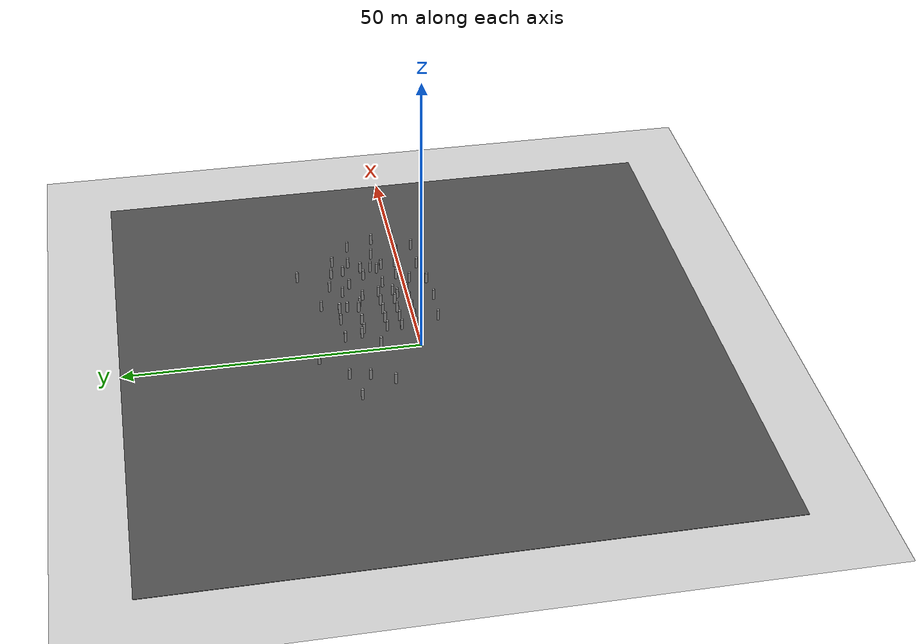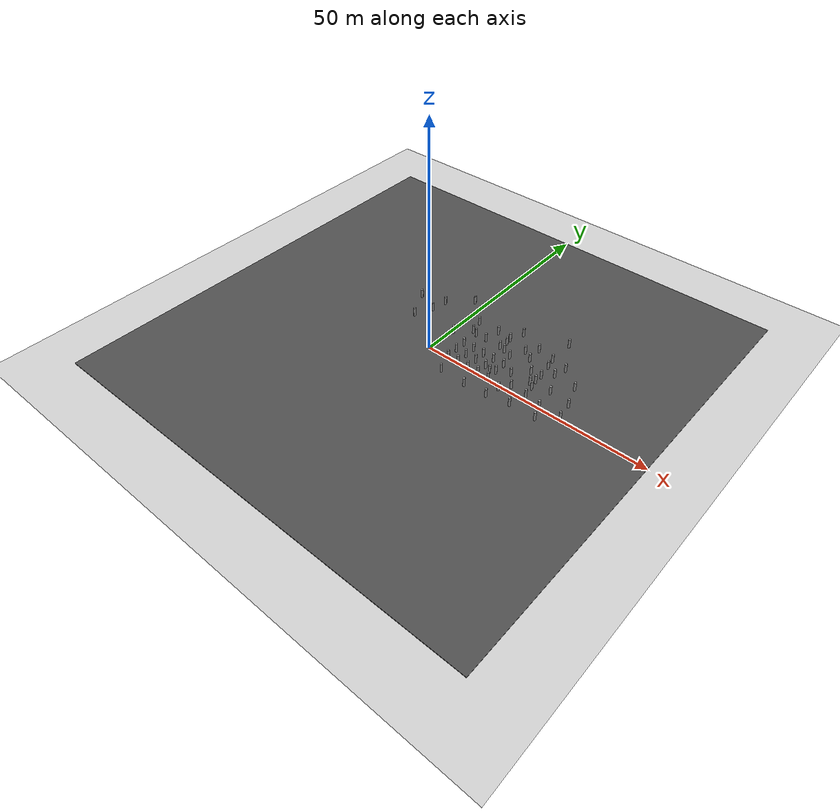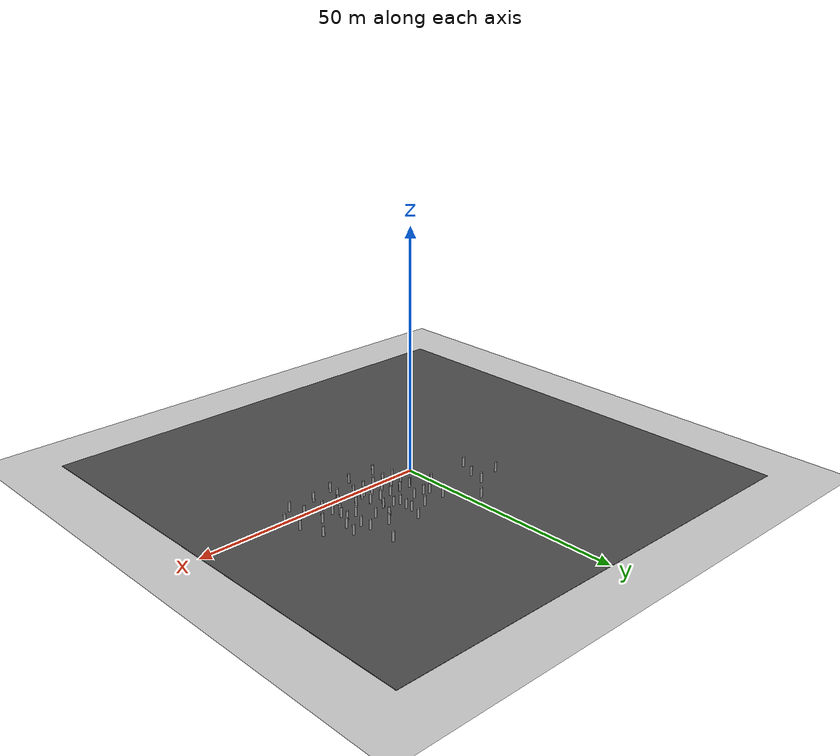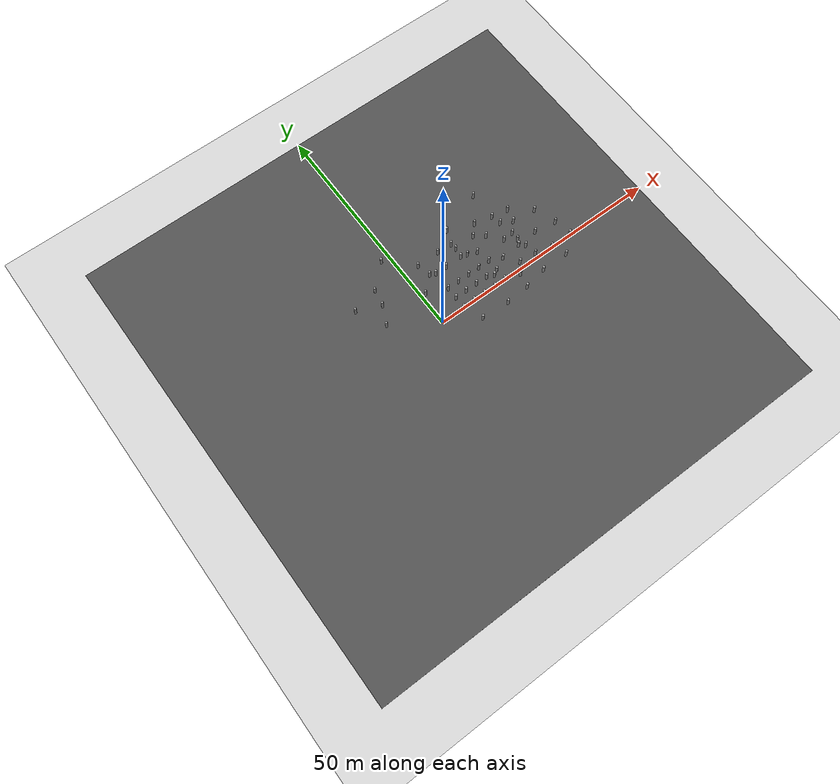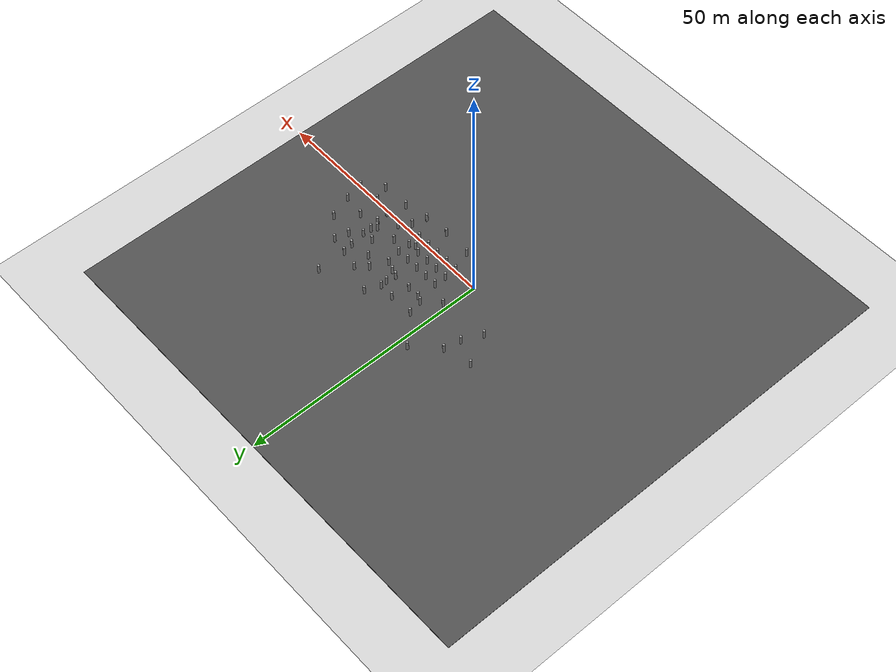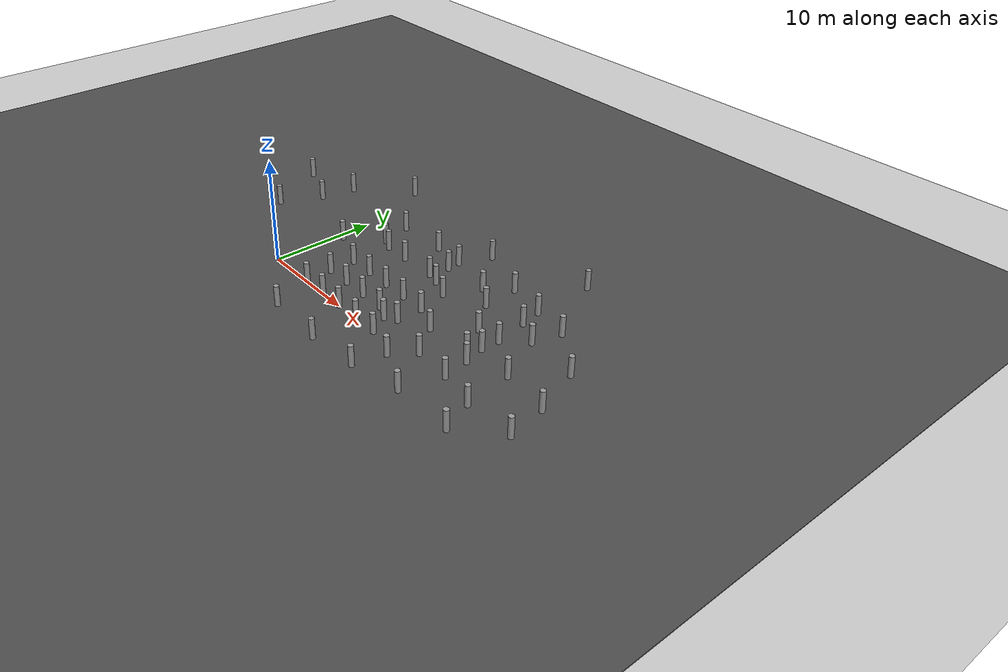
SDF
<sdf version="1.6">
 <world name="default">
  <light name="sun" type="directional">
   <pose>0 0 10 0 -0 0</pose>
   <diffuse>0.8 0.8 0.8 1</diffuse>
   <specular>0.1 0.1 0.1 1</specular>
   <attenuation>
    <range>1000</range>
    <constant>0.9</constant>
    <linear>0.01</linear>
    <quadratic>0.001</quadratic>
   </attenuation>
   <direction>-0.5 0.5 -1</direction>
  </light>
  <model name="ground_plane">
   <static>1</static>
   <link name="link">
    <collision name="collision">
     <geometry><plane><normal>0 0 1</normal><size>100 100</size></plane></geometry>
     <surface><friction><ode><mu>100</mu><mu2>50</mu2></ode></friction></surface>
    </collision>
    <visual name="visual">
     <cast_shadows>0</cast_shadows>
     <geometry><plane><normal>0 0 1</normal><size>100 100</size></plane></geometry>
     <material>
      <script><uri>file://media/materials/scripts/gazebo.material</uri><name>Gazebo/Grey</name></script>
     </material>
    </visual>
   </link>
  </model>
  <physics name="default_physics" default="0" type="ode">
   <ode>
    <solver>
     <type>quick</type>
     <iters>10</iters>
     <sor>1.3</sor>
     <use_dynamic_moi_rescaling>0</use_dynamic_moi_rescaling>
    </solver>
    <constraints>
     <cfm>0</cfm>
     <erp>0.2</erp>
     <contact_max_correcting_vel>100</contact_max_correcting_vel>
     <contact_surface_layer>0.001</contact_surface_layer>
    </constraints>
   </ode>
   <max_step_size>0.002</max_step_size>
   <real_time_factor>1</real_time_factor>
   <real_time_update_rate>500</real_time_update_rate>
  </physics>
  <gravity>0 0 -9.8066</gravity>
  <magnetic_field>6e-06 2.3e-05 -4.2e-05</magnetic_field>
  <atmosphere type="adiabatic"/>
  <scene><ambient>0.4 0.4 0.4 1</ambient><background>0.7 0.7 0.7 1</background><shadows>1</shadows></scene>
  <spherical_coordinates>
   <surface_model>EARTH_WGS84</surface_model>
   <latitude_deg>0</latitude_deg>
   <longitude_deg>0</longitude_deg>
   <elevation>0</elevation>
   <heading_deg>0</heading_deg>
  </spherical_coordinates>
  <model name="asphalt_plane_0">
   <link name="link">
    <inertial>
     <mass>1</mass>
     <inertia><ixx>1</ixx><ixy>0</ixy><ixz>0</ixz><iyy>1</iyy><iyz>0</iyz><izz>1</izz></inertia>
    </inertial>
    <visual name="visual">
     <cast_shadows>0</cast_shadows>
     <geometry><box><size>100 100 0.1</size></box></geometry>
     <material>
      <script>
       <uri>model://asphalt_plane/materials/scripts</uri>
       <uri>model://asphalt_plane/materials/textures</uri>
       <name>vrc/asphalt</name>
      </script>
      <ambient>0.5 0.5 0.5 1</ambient>
      <diffuse>0.5 0.5 0.5 1</diffuse>
      <specular>0.2 0.2 0.2 1</specular>
      <emissive>0 0 0 1</emissive>
      <shader type="vertex"><normal_map>__default__</normal_map></shader>
     </material>
    </visual>
    <collision name="collision">
     <geometry><box><size>100 100 0.1</size></box></geometry>
     <surface>
      <friction>
       <ode><mu>1</mu><mu2>1</mu2><fdir1>0 0 0</fdir1><slip1>0</slip1><slip2>0</slip2></ode>
       <torsional>
        <coefficient>1</coefficient>
        <patch_radius>0</patch_radius>
        <surface_radius>0</surface_radius>
        <use_patch_radius>1</use_patch_radius>
        <ode><slip>0</slip></ode>
       </torsional>
      </friction>
      <bounce><restitution_coefficient>0</restitution_coefficient><threshold>1e+06</threshold></bounce>
      <contact>
       <collide_without_contact>0</collide_without_contact>
       <collide_without_contact_bitmask>1</collide_without_contact_bitmask>
       <collide_bitmask>1</collide_bitmask>
       <ode>
        <soft_cfm>0</soft_cfm>
        <soft_erp>0.2</soft_erp>
        <kp>1e+13</kp>
        <kd>1</kd>
        <max_vel>0.01</max_vel>
        <min_depth>0</min_depth>
       </ode>
       <bullet>
        <split_impulse>1</split_impulse>
        <split_impulse_penetration_threshold>-0.01</split_impulse_penetration_threshold>
        <soft_cfm>0</soft_cfm>
        <soft_erp>0.2</soft_erp>
        <kp>1e+13</kp>
        <kd>1</kd>
       </bullet>
      </contact>
     </surface>
    </collision>
   </link>
   <static>1</static>
   <pose>-0.137833 0.204655 0 0 -0 0</pose>
  </model>
  <model name="vps_sim_obstacle">
   <link name="link">
    <inertial>
     <mass>1</mass>
     <inertia><ixx>0.145833</ixx><ixy>0</ixy><ixz>0</ixz><iyy>0.145833</iyy><iyz>0</iyz><izz>0.125</izz></inertia>
    </inertial>
    <visual name="visual">
     <geometry><cylinder><radius>0.25</radius><length>2</length></cylinder></geometry>
     <material>
      <script><name>Gazebo/Grey</name><uri>file://media/materials/scripts/gazebo.material</uri></script>
      <ambient>0.3 0.3 0.3 1</ambient>
      <diffuse>0.7 0.7 0.7 1</diffuse>
      <specular>0.01 0.01 0.01 1</specular>
      <emissive>0 0 0 1</emissive>
      <shader type="vertex"><normal_map>__default__</normal_map></shader>
     </material>
    </visual>
    <collision name="collision">
     <geometry><cylinder><radius>0.25</radius><length>2</length></cylinder></geometry>
     <surface>
      <friction>
       <ode><mu>1</mu><mu2>1</mu2><fdir1>0 0 0</fdir1><slip1>0</slip1><slip2>0</slip2></ode>
       <torsional>
        <coefficient>1</coefficient>
        <patch_radius>0</patch_radius>
        <surface_radius>0</surface_radius>
        <use_patch_radius>1</use_patch_radius>
        <ode><slip>0</slip></ode>
       </torsional>
      </friction>
      <bounce><restitution_coefficient>0</restitution_coefficient><threshold>1e+06</threshold></bounce>
      <contact>
       <collide_without_contact>0</collide_without_contact>
       <collide_without_contact_bitmask>1</collide_without_contact_bitmask>
       <collide_bitmask>1</collide_bitmask>
       <ode>
        <soft_cfm>0</soft_cfm>
        <soft_erp>0.2</soft_erp>
        <kp>1e+13</kp>
        <kd>1</kd>
        <max_vel>0.01</max_vel>
        <min_depth>0</min_depth>
       </ode>
       <bullet>
        <split_impulse>1</split_impulse>
        <split_impulse_penetration_threshold>-0.01</split_impulse_penetration_threshold>
        <soft_cfm>0</soft_cfm>
        <soft_erp>0.2</soft_erp>
        <kp>1e+13</kp>
        <kd>1</kd>
       </bullet>
      </contact>
     </surface>
    </collision>
   </link>
   <static>0</static>
   <pose>5.00167 -0.001811 1.05001 -1.9e-05 8e-06 0.033451</pose>
  </model>
  <model name="vps_sim_obstacle_1">
   <link name="link">
    <inertial>
     <mass>1</mass>
     <inertia><ixx>0.145833</ixx><ixy>0</ixy><ixz>0</ixz><iyy>0.145833</iyy><iyz>0</iyz><izz>0.125</izz></inertia>
    </inertial>
    <visual name="visual">
     <geometry><cylinder><radius>0.25</radius><length>2</length></cylinder></geometry>
     <material>
      <script><name>Gazebo/Grey</name><uri>file://media/materials/scripts/gazebo.material</uri></script>
      <ambient>0.3 0.3 0.3 1</ambient>
      <diffuse>0.7 0.7 0.7 1</diffuse>
      <specular>0.01 0.01 0.01 1</specular>
      <emissive>0 0 0 1</emissive>
      <shader type="vertex"><normal_map>__default__</normal_map></shader>
     </material>
    </visual>
    <collision name="collision">
     <geometry><cylinder><radius>0.25</radius><length>2</length></cylinder></geometry>
     <surface>
      <friction>
       <ode><mu>1</mu><mu2>1</mu2><fdir1>0 0 0</fdir1><slip1>0</slip1><slip2>0</slip2></ode>
       <torsional>
        <coefficient>1</coefficient>
        <patch_radius>0</patch_radius>
        <surface_radius>0</surface_radius>
        <use_patch_radius>1</use_patch_radius>
        <ode><slip>0</slip></ode>
       </torsional>
      </friction>
      <bounce><restitution_coefficient>0</restitution_coefficient><threshold>1e+06</threshold></bounce>
      <contact>
       <collide_without_contact>0</collide_without_contact>
       <collide_without_contact_bitmask>1</collide_without_contact_bitmask>
       <collide_bitmask>1</collide_bitmask>
       <ode>
        <soft_cfm>0</soft_cfm>
        <soft_erp>0.2</soft_erp>
        <kp>1e+13</kp>
        <kd>1</kd>
        <max_vel>0.01</max_vel>
        <min_depth>0</min_depth>
       </ode>
       <bullet>
        <split_impulse>1</split_impulse>
        <split_impulse_penetration_threshold>-0.01</split_impulse_penetration_threshold>
        <soft_cfm>0</soft_cfm>
        <soft_erp>0.2</soft_erp>
        <kp>1e+13</kp>
        <kd>1</kd>
       </bullet>
      </contact>
     </surface>
    </collision>
   </link>
   <static>0</static>
   <pose>5.00232 8.99749 1.04999 -2.7e-05 1.8e-05 0.034468</pose>
  </model>
  <model name="vps_sim_obstacle_2">
   <link name="link">
    <inertial>
     <mass>1</mass>
     <inertia><ixx>0.145833</ixx><ixy>0</ixy><ixz>0</ixz><iyy>0.145833</iyy><iyz>0</iyz><izz>0.125</izz></inertia>
    </inertial>
    <visual name="visual">
     <geometry><cylinder><radius>0.25</radius><length>2</length></cylinder></geometry>
     <material>
      <script><name>Gazebo/Grey</name><uri>file://media/materials/scripts/gazebo.material</uri></script>
      <ambient>0.3 0.3 0.3 1</ambient>
      <diffuse>0.7 0.7 0.7 1</diffuse>
      <specular>0.01 0.01 0.01 1</specular>
      <emissive>0 0 0 1</emissive>
      <shader type="vertex"><normal_map>__default__</normal_map></shader>
     </material>
    </visual>
    <collision name="collision">
     <geometry><cylinder><radius>0.25</radius><length>2</length></cylinder></geometry>
     <surface>
      <friction>
       <ode><mu>1</mu><mu2>1</mu2><fdir1>0 0 0</fdir1><slip1>0</slip1><slip2>0</slip2></ode>
       <torsional>
        <coefficient>1</coefficient>
        <patch_radius>0</patch_radius>
        <surface_radius>0</surface_radius>
        <use_patch_radius>1</use_patch_radius>
        <ode><slip>0</slip></ode>
       </torsional>
      </friction>
      <bounce><restitution_coefficient>0</restitution_coefficient><threshold>1e+06</threshold></bounce>
      <contact>
       <collide_without_contact>0</collide_without_contact>
       <collide_without_contact_bitmask>1</collide_without_contact_bitmask>
       <collide_bitmask>1</collide_bitmask>
       <ode>
        <soft_cfm>0</soft_cfm>
        <soft_erp>0.2</soft_erp>
        <kp>1e+13</kp>
        <kd>1</kd>
        <max_vel>0.01</max_vel>
        <min_depth>0</min_depth>
       </ode>
       <bullet>
        <split_impulse>1</split_impulse>
        <split_impulse_penetration_threshold>-0.01</split_impulse_penetration_threshold>
        <soft_cfm>0</soft_cfm>
        <soft_erp>0.2</soft_erp>
        <kp>1e+13</kp>
        <kd>1</kd>
       </bullet>
      </contact>
     </surface>
    </collision>
   </link>
   <static>0</static>
   <pose>7.50166 -0.001786 1.04996 -1e-06 3e-06 0.0403</pose>
  </model>
  <model name="vps_sim_obstacle_3">
   <link name="link">
    <inertial>
     <mass>1</mass>
     <inertia><ixx>0.145833</ixx><ixy>0</ixy><ixz>0</ixz><iyy>0.145833</iyy><iyz>0</iyz><izz>0.125</izz></inertia>
    </inertial>
    <visual name="visual">
     <geometry><cylinder><radius>0.25</radius><length>2</length></cylinder></geometry>
     <material>
      <script><name>Gazebo/Grey</name><uri>file://media/materials/scripts/gazebo.material</uri></script>
      <ambient>0.3 0.3 0.3 1</ambient>
      <diffuse>0.7 0.7 0.7 1</diffuse>
      <specular>0.01 0.01 0.01 1</specular>
      <emissive>0 0 0 1</emissive>
      <shader type="vertex"><normal_map>__default__</normal_map></shader>
     </material>
    </visual>
    <collision name="collision">
     <geometry><cylinder><radius>0.25</radius><length>2</length></cylinder></geometry>
     <surface>
      <friction>
       <ode><mu>1</mu><mu2>1</mu2><fdir1>0 0 0</fdir1><slip1>0</slip1><slip2>0</slip2></ode>
       <torsional>
        <coefficient>1</coefficient>
        <patch_radius>0</patch_radius>
        <surface_radius>0</surface_radius>
        <use_patch_radius>1</use_patch_radius>
        <ode><slip>0</slip></ode>
       </torsional>
      </friction>
      <bounce><restitution_coefficient>0</restitution_coefficient><threshold>1e+06</threshold></bounce>
      <contact>
       <collide_without_contact>0</collide_without_contact>
       <collide_without_contact_bitmask>1</collide_without_contact_bitmask>
       <collide_bitmask>1</collide_bitmask>
       <ode>
        <soft_cfm>0</soft_cfm>
        <soft_erp>0.2</soft_erp>
        <kp>1e+13</kp>
        <kd>1</kd>
        <max_vel>0.01</max_vel>
        <min_depth>0</min_depth>
       </ode>
       <bullet>
        <split_impulse>1</split_impulse>
        <split_impulse_penetration_threshold>-0.01</split_impulse_penetration_threshold>
        <soft_cfm>0</soft_cfm>
        <soft_erp>0.2</soft_erp>
        <kp>1e+13</kp>
        <kd>1</kd>
       </bullet>
      </contact>
     </surface>
    </collision>
   </link>
   <static>0</static>
   <pose>10.0017 -0.001874 1.05001 -4.7e-05 2e-05 0.041216</pose>
  </model>
  <model name="vps_sim_obstacle_4">
   <link name="link">
    <inertial>
     <mass>1</mass>
     <inertia><ixx>0.145833</ixx><ixy>0</ixy><ixz>0</ixz><iyy>0.145833</iyy><iyz>0</iyz><izz>0.125</izz></inertia>
    </inertial>
    <visual name="visual">
     <geometry><cylinder><radius>0.25</radius><length>2</length></cylinder></geometry>
     <material>
      <script><name>Gazebo/Grey</name><uri>file://media/materials/scripts/gazebo.material</uri></script>
      <ambient>0.3 0.3 0.3 1</ambient>
      <diffuse>0.7 0.7 0.7 1</diffuse>
      <specular>0.01 0.01 0.01 1</specular>
      <emissive>0 0 0 1</emissive>
      <shader type="vertex"><normal_map>__default__</normal_map></shader>
     </material>
    </visual>
    <collision name="collision">
     <geometry><cylinder><radius>0.25</radius><length>2</length></cylinder></geometry>
     <surface>
      <friction>
       <ode><mu>1</mu><mu2>1</mu2><fdir1>0 0 0</fdir1><slip1>0</slip1><slip2>0</slip2></ode>
       <torsional>
        <coefficient>1</coefficient>
        <patch_radius>0</patch_radius>
        <surface_radius>0</surface_radius>
        <use_patch_radius>1</use_patch_radius>
        <ode><slip>0</slip></ode>
       </torsional>
      </friction>
      <bounce><restitution_coefficient>0</restitution_coefficient><threshold>1e+06</threshold></bounce>
      <contact>
       <collide_without_contact>0</collide_without_contact>
       <collide_without_contact_bitmask>1</collide_without_contact_bitmask>
       <collide_bitmask>1</collide_bitmask>
       <ode>
        <soft_cfm>0</soft_cfm>
        <soft_erp>0.2</soft_erp>
        <kp>1e+13</kp>
        <kd>1</kd>
        <max_vel>0.01</max_vel>
        <min_depth>0</min_depth>
       </ode>
       <bullet>
        <split_impulse>1</split_impulse>
        <split_impulse_penetration_threshold>-0.01</split_impulse_penetration_threshold>
        <soft_cfm>0</soft_cfm>
        <soft_erp>0.2</soft_erp>
        <kp>1e+13</kp>
        <kd>1</kd>
       </bullet>
      </contact>
     </surface>
    </collision>
   </link>
   <static>0</static>
   <pose>12.5016 -0.00191 1.04997 -1.8e-05 8e-06 0.044598</pose>
  </model>
  <model name="vps_sim_obstacle_5">
   <link name="link">
    <inertial>
     <mass>1</mass>
     <inertia><ixx>0.145833</ixx><ixy>0</ixy><ixz>0</ixz><iyy>0.145833</iyy><iyz>0</iyz><izz>0.125</izz></inertia>
    </inertial>
    <visual name="visual">
     <geometry><cylinder><radius>0.25</radius><length>2</length></cylinder></geometry>
     <material>
      <script><name>Gazebo/Grey</name><uri>file://media/materials/scripts/gazebo.material</uri></script>
      <ambient>0.3 0.3 0.3 1</ambient>
      <diffuse>0.7 0.7 0.7 1</diffuse>
      <specular>0.01 0.01 0.01 1</specular>
      <emissive>0 0 0 1</emissive>
      <shader type="vertex"><normal_map>__default__</normal_map></shader>
     </material>
    </visual>
    <collision name="collision">
     <geometry><cylinder><radius>0.25</radius><length>2</length></cylinder></geometry>
     <surface>
      <friction>
       <ode><mu>1</mu><mu2>1</mu2><fdir1>0 0 0</fdir1><slip1>0</slip1><slip2>0</slip2></ode>
       <torsional>
        <coefficient>1</coefficient>
        <patch_radius>0</patch_radius>
        <surface_radius>0</surface_radius>
        <use_patch_radius>1</use_patch_radius>
        <ode><slip>0</slip></ode>
       </torsional>
      </friction>
      <bounce><restitution_coefficient>0</restitution_coefficient><threshold>1e+06</threshold></bounce>
      <contact>
       <collide_without_contact>0</collide_without_contact>
       <collide_without_contact_bitmask>1</collide_without_contact_bitmask>
       <collide_bitmask>1</collide_bitmask>
       <ode>
        <soft_cfm>0</soft_cfm>
        <soft_erp>0.2</soft_erp>
        <kp>1e+13</kp>
        <kd>1</kd>
        <max_vel>0.01</max_vel>
        <min_depth>0</min_depth>
       </ode>
       <bullet>
        <split_impulse>1</split_impulse>
        <split_impulse_penetration_threshold>-0.01</split_impulse_penetration_threshold>
        <soft_cfm>0</soft_cfm>
        <soft_erp>0.2</soft_erp>
        <kp>1e+13</kp>
        <kd>1</kd>
       </bullet>
      </contact>
     </surface>
    </collision>
   </link>
   <static>0</static>
   <pose>15.0022 -0.001932 1.04997 -1.8e-05 2.4e-05 0.028864</pose>
  </model>
  <model name="vps_sim_obstacle_6">
   <link name="link">
    <inertial>
     <mass>1</mass>
     <inertia><ixx>0.145833</ixx><ixy>0</ixy><ixz>0</ixz><iyy>0.145833</iyy><iyz>0</iyz><izz>0.125</izz></inertia>
    </inertial>
    <visual name="visual">
     <geometry><cylinder><radius>0.25</radius><length>2</length></cylinder></geometry>
     <material>
      <script><name>Gazebo/Grey</name><uri>file://media/materials/scripts/gazebo.material</uri></script>
      <ambient>0.3 0.3 0.3 1</ambient>
      <diffuse>0.7 0.7 0.7 1</diffuse>
      <specular>0.01 0.01 0.01 1</specular>
      <emissive>0 0 0 1</emissive>
      <shader type="vertex"><normal_map>__default__</normal_map></shader>
     </material>
    </visual>
    <collision name="collision">
     <geometry><cylinder><radius>0.25</radius><length>2</length></cylinder></geometry>
     <surface>
      <friction>
       <ode><mu>1</mu><mu2>1</mu2><fdir1>0 0 0</fdir1><slip1>0</slip1><slip2>0</slip2></ode>
       <torsional>
        <coefficient>1</coefficient>
        <patch_radius>0</patch_radius>
        <surface_radius>0</surface_radius>
        <use_patch_radius>1</use_patch_radius>
        <ode><slip>0</slip></ode>
       </torsional>
      </friction>
      <bounce><restitution_coefficient>0</restitution_coefficient><threshold>1e+06</threshold></bounce>
      <contact>
       <collide_without_contact>0</collide_without_contact>
       <collide_without_contact_bitmask>1</collide_without_contact_bitmask>
       <collide_bitmask>1</collide_bitmask>
       <ode>
        <soft_cfm>0</soft_cfm>
        <soft_erp>0.2</soft_erp>
        <kp>1e+13</kp>
        <kd>1</kd>
        <max_vel>0.01</max_vel>
        <min_depth>0</min_depth>
       </ode>
       <bullet>
        <split_impulse>1</split_impulse>
        <split_impulse_penetration_threshold>-0.01</split_impulse_penetration_threshold>
        <soft_cfm>0</soft_cfm>
        <soft_erp>0.2</soft_erp>
        <kp>1e+13</kp>
        <kd>1</kd>
       </bullet>
      </contact>
     </surface>
    </collision>
   </link>
   <static>0</static>
   <pose>5.00177 2.49792 1.04997 -1.6e-05 2e-05 0.032816</pose>
  </model>
  <model name="vps_sim_obstacle_7">
   <link name="link">
    <inertial>
     <mass>1</mass>
     <inertia><ixx>0.145833</ixx><ixy>0</ixy><ixz>0</ixz><iyy>0.145833</iyy><iyz>0</iyz><izz>0.125</izz></inertia>
    </inertial>
    <visual name="visual">
     <geometry><cylinder><radius>0.25</radius><length>2</length></cylinder></geometry>
     <material>
      <script><name>Gazebo/Grey</name><uri>file://media/materials/scripts/gazebo.material</uri></script>
      <ambient>0.3 0.3 0.3 1</ambient>
      <diffuse>0.7 0.7 0.7 1</diffuse>
      <specular>0.01 0.01 0.01 1</specular>
      <emissive>0 0 0 1</emissive>
      <shader type="vertex"><normal_map>__default__</normal_map></shader>
     </material>
    </visual>
    <collision name="collision">
     <geometry><cylinder><radius>0.25</radius><length>2</length></cylinder></geometry>
     <surface>
      <friction>
       <ode><mu>1</mu><mu2>1</mu2><fdir1>0 0 0</fdir1><slip1>0</slip1><slip2>0</slip2></ode>
       <torsional>
        <coefficient>1</coefficient>
        <patch_radius>0</patch_radius>
        <surface_radius>0</surface_radius>
        <use_patch_radius>1</use_patch_radius>
        <ode><slip>0</slip></ode>
       </torsional>
      </friction>
      <bounce><restitution_coefficient>0</restitution_coefficient><threshold>1e+06</threshold></bounce>
      <contact>
       <collide_without_contact>0</collide_without_contact>
       <collide_without_contact_bitmask>1</collide_without_contact_bitmask>
       <collide_bitmask>1</collide_bitmask>
       <ode>
        <soft_cfm>0</soft_cfm>
        <soft_erp>0.2</soft_erp>
        <kp>1e+13</kp>
        <kd>1</kd>
        <max_vel>0.01</max_vel>
        <min_depth>0</min_depth>
       </ode>
       <bullet>
        <split_impulse>1</split_impulse>
        <split_impulse_penetration_threshold>-0.01</split_impulse_penetration_threshold>
        <soft_cfm>0</soft_cfm>
        <soft_erp>0.2</soft_erp>
        <kp>1e+13</kp>
        <kd>1</kd>
       </bullet>
      </contact>
     </surface>
    </collision>
   </link>
   <static>0</static>
   <pose>7.50156 2.49795 1.05 0 6e-06 0.041498</pose>
  </model>
  <model name="vps_sim_obstacle_8">
   <link name="link">
    <inertial>
     <mass>1</mass>
     <inertia><ixx>0.145833</ixx><ixy>0</ixy><ixz>0</ixz><iyy>0.145833</iyy><iyz>0</iyz><izz>0.125</izz></inertia>
    </inertial>
    <visual name="visual">
     <geometry><cylinder><radius>0.25</radius><length>2</length></cylinder></geometry>
     <material>
      <script><name>Gazebo/Grey</name><uri>file://media/materials/scripts/gazebo.material</uri></script>
      <ambient>0.3 0.3 0.3 1</ambient>
      <diffuse>0.7 0.7 0.7 1</diffuse>
      <specular>0.01 0.01 0.01 1</specular>
      <emissive>0 0 0 1</emissive>
      <shader type="vertex"><normal_map>__default__</normal_map></shader>
     </material>
    </visual>
    <collision name="collision">
     <geometry><cylinder><radius>0.25</radius><length>2</length></cylinder></geometry>
     <surface>
      <friction>
       <ode><mu>1</mu><mu2>1</mu2><fdir1>0 0 0</fdir1><slip1>0</slip1><slip2>0</slip2></ode>
       <torsional>
        <coefficient>1</coefficient>
        <patch_radius>0</patch_radius>
        <surface_radius>0</surface_radius>
        <use_patch_radius>1</use_patch_radius>
        <ode><slip>0</slip></ode>
       </torsional>
      </friction>
      <bounce><restitution_coefficient>0</restitution_coefficient><threshold>1e+06</threshold></bounce>
      <contact>
       <collide_without_contact>0</collide_without_contact>
       <collide_without_contact_bitmask>1</collide_without_contact_bitmask>
       <collide_bitmask>1</collide_bitmask>
       <ode>
        <soft_cfm>0</soft_cfm>
        <soft_erp>0.2</soft_erp>
        <kp>1e+13</kp>
        <kd>1</kd>
        <max_vel>0.01</max_vel>
        <min_depth>0</min_depth>
       </ode>
       <bullet>
        <split_impulse>1</split_impulse>
        <split_impulse_penetration_threshold>-0.01</split_impulse_penetration_threshold>
        <soft_cfm>0</soft_cfm>
        <soft_erp>0.2</soft_erp>
        <kp>1e+13</kp>
        <kd>1</kd>
       </bullet>
      </contact>
     </surface>
    </collision>
   </link>
   <static>0</static>
   <pose>10.0016 2.49806 1.04998 7e-06 1e-06 0.045175</pose>
  </model>
  <model name="vps_sim_obstacle_9">
   <link name="link">
    <inertial>
     <mass>1</mass>
     <inertia><ixx>0.145833</ixx><ixy>0</ixy><ixz>0</ixz><iyy>0.145833</iyy><iyz>0</iyz><izz>0.125</izz></inertia>
    </inertial>
    <visual name="visual">
     <geometry><cylinder><radius>0.25</radius><length>2</length></cylinder></geometry>
     <material>
      <script><name>Gazebo/Grey</name><uri>file://media/materials/scripts/gazebo.material</uri></script>
      <ambient>0.3 0.3 0.3 1</ambient>
      <diffuse>0.7 0.7 0.7 1</diffuse>
      <specular>0.01 0.01 0.01 1</specular>
      <emissive>0 0 0 1</emissive>
      <shader type="vertex"><normal_map>__default__</normal_map></shader>
     </material>
    </visual>
    <collision name="collision">
     <geometry><cylinder><radius>0.25</radius><length>2</length></cylinder></geometry>
     <surface>
      <friction>
       <ode><mu>1</mu><mu2>1</mu2><fdir1>0 0 0</fdir1><slip1>0</slip1><slip2>0</slip2></ode>
       <torsional>
        <coefficient>1</coefficient>
        <patch_radius>0</patch_radius>
        <surface_radius>0</surface_radius>
        <use_patch_radius>1</use_patch_radius>
        <ode><slip>0</slip></ode>
       </torsional>
      </friction>
      <bounce><restitution_coefficient>0</restitution_coefficient><threshold>1e+06</threshold></bounce>
      <contact>
       <collide_without_contact>0</collide_without_contact>
       <collide_without_contact_bitmask>1</collide_without_contact_bitmask>
       <collide_bitmask>1</collide_bitmask>
       <ode>
        <soft_cfm>0</soft_cfm>
        <soft_erp>0.2</soft_erp>
        <kp>1e+13</kp>
        <kd>1</kd>
        <max_vel>0.01</max_vel>
        <min_depth>0</min_depth>
       </ode>
       <bullet>
        <split_impulse>1</split_impulse>
        <split_impulse_penetration_threshold>-0.01</split_impulse_penetration_threshold>
        <soft_cfm>0</soft_cfm>
        <soft_erp>0.2</soft_erp>
        <kp>1e+13</kp>
        <kd>1</kd>
       </bullet>
      </contact>
     </surface>
    </collision>
   </link>
   <static>0</static>
   <pose>12.5021 2.49773 1.04997 1.1e-05 -1e-05 0.038836</pose>
  </model>
  <model name="vps_sim_obstacle_10">
   <link name="link">
    <inertial>
     <mass>1</mass>
     <inertia><ixx>0.145833</ixx><ixy>0</ixy><ixz>0</ixz><iyy>0.145833</iyy><iyz>0</iyz><izz>0.125</izz></inertia>
    </inertial>
    <visual name="visual">
     <geometry><cylinder><radius>0.25</radius><length>2</length></cylinder></geometry>
     <material>
      <script><name>Gazebo/Grey</name><uri>file://media/materials/scripts/gazebo.material</uri></script>
      <ambient>0.3 0.3 0.3 1</ambient>
      <diffuse>0.7 0.7 0.7 1</diffuse>
      <specular>0.01 0.01 0.01 1</specular>
      <emissive>0 0 0 1</emissive>
      <shader type="vertex"><normal_map>__default__</normal_map></shader>
     </material>
    </visual>
    <collision name="collision">
     <geometry><cylinder><radius>0.25</radius><length>2</length></cylinder></geometry>
     <surface>
      <friction>
       <ode><mu>1</mu><mu2>1</mu2><fdir1>0 0 0</fdir1><slip1>0</slip1><slip2>0</slip2></ode>
       <torsional>
        <coefficient>1</coefficient>
        <patch_radius>0</patch_radius>
        <surface_radius>0</surface_radius>
        <use_patch_radius>1</use_patch_radius>
        <ode><slip>0</slip></ode>
       </torsional>
      </friction>
      <bounce><restitution_coefficient>0</restitution_coefficient><threshold>1e+06</threshold></bounce>
      <contact>
       <collide_without_contact>0</collide_without_contact>
       <collide_without_contact_bitmask>1</collide_without_contact_bitmask>
       <collide_bitmask>1</collide_bitmask>
       <ode>
        <soft_cfm>0</soft_cfm>
        <soft_erp>0.2</soft_erp>
        <kp>1e+13</kp>
        <kd>1</kd>
        <max_vel>0.01</max_vel>
        <min_depth>0</min_depth>
       </ode>
       <bullet>
        <split_impulse>1</split_impulse>
        <split_impulse_penetration_threshold>-0.01</split_impulse_penetration_threshold>
        <soft_cfm>0</soft_cfm>
        <soft_erp>0.2</soft_erp>
        <kp>1e+13</kp>
        <kd>1</kd>
       </bullet>
      </contact>
     </surface>
    </collision>
   </link>
   <static>0</static>
   <pose>15.0023 2.49798 1.05001 -1.3e-05 2.2e-05 0.044878</pose>
  </model>
  <model name="vps_sim_obstacle_11">
   <link name="link">
    <inertial>
     <mass>1</mass>
     <inertia><ixx>0.145833</ixx><ixy>0</ixy><ixz>0</ixz><iyy>0.145833</iyy><iyz>0</iyz><izz>0.125</izz></inertia>
    </inertial>
    <visual name="visual">
     <geometry><cylinder><radius>0.25</radius><length>2</length></cylinder></geometry>
     <material>
      <script><name>Gazebo/Grey</name><uri>file://media/materials/scripts/gazebo.material</uri></script>
      <ambient>0.3 0.3 0.3 1</ambient>
      <diffuse>0.7 0.7 0.7 1</diffuse>
      <specular>0.01 0.01 0.01 1</specular>
      <emissive>0 0 0 1</emissive>
      <shader type="vertex"><normal_map>__default__</normal_map></shader>
     </material>
    </visual>
    <collision name="collision">
     <geometry><cylinder><radius>0.25</radius><length>2</length></cylinder></geometry>
     <surface>
      <friction>
       <ode><mu>1</mu><mu2>1</mu2><fdir1>0 0 0</fdir1><slip1>0</slip1><slip2>0</slip2></ode>
       <torsional>
        <coefficient>1</coefficient>
        <patch_radius>0</patch_radius>
        <surface_radius>0</surface_radius>
        <use_patch_radius>1</use_patch_radius>
        <ode><slip>0</slip></ode>
       </torsional>
      </friction>
      <bounce><restitution_coefficient>0</restitution_coefficient><threshold>1e+06</threshold></bounce>
      <contact>
       <collide_without_contact>0</collide_without_contact>
       <collide_without_contact_bitmask>1</collide_without_contact_bitmask>
       <collide_bitmask>1</collide_bitmask>
       <ode>
        <soft_cfm>0</soft_cfm>
        <soft_erp>0.2</soft_erp>
        <kp>1e+13</kp>
        <kd>1</kd>
        <max_vel>0.01</max_vel>
        <min_depth>0</min_depth>
       </ode>
       <bullet>
        <split_impulse>1</split_impulse>
        <split_impulse_penetration_threshold>-0.01</split_impulse_penetration_threshold>
        <soft_cfm>0</soft_cfm>
        <soft_erp>0.2</soft_erp>
        <kp>1e+13</kp>
        <kd>1</kd>
       </bullet>
      </contact>
     </surface>
    </collision>
   </link>
   <static>0</static>
   <pose>5.00194 4.99772 1.04996 -4e-06 4e-06 0.019612</pose>
  </model>
  <model name="vps_sim_obstacle_12">
   <link name="link">
    <inertial>
     <mass>1</mass>
     <inertia><ixx>0.145833</ixx><ixy>0</ixy><ixz>0</ixz><iyy>0.145833</iyy><iyz>0</iyz><izz>0.125</izz></inertia>
    </inertial>
    <visual name="visual">
     <geometry><cylinder><radius>0.25</radius><length>2</length></cylinder></geometry>
     <material>
      <script><name>Gazebo/Grey</name><uri>file://media/materials/scripts/gazebo.material</uri></script>
      <ambient>0.3 0.3 0.3 1</ambient>
      <diffuse>0.7 0.7 0.7 1</diffuse>
      <specular>0.01 0.01 0.01 1</specular>
      <emissive>0 0 0 1</emissive>
      <shader type="vertex"><normal_map>__default__</normal_map></shader>
     </material>
    </visual>
    <collision name="collision">
     <geometry><cylinder><radius>0.25</radius><length>2</length></cylinder></geometry>
     <surface>
      <friction>
       <ode><mu>1</mu><mu2>1</mu2><fdir1>0 0 0</fdir1><slip1>0</slip1><slip2>0</slip2></ode>
       <torsional>
        <coefficient>1</coefficient>
        <patch_radius>0</patch_radius>
        <surface_radius>0</surface_radius>
        <use_patch_radius>1</use_patch_radius>
        <ode><slip>0</slip></ode>
       </torsional>
      </friction>
      <bounce><restitution_coefficient>0</restitution_coefficient><threshold>1e+06</threshold></bounce>
      <contact>
       <collide_without_contact>0</collide_without_contact>
       <collide_without_contact_bitmask>1</collide_without_contact_bitmask>
       <collide_bitmask>1</collide_bitmask>
       <ode>
        <soft_cfm>0</soft_cfm>
        <soft_erp>0.2</soft_erp>
        <kp>1e+13</kp>
        <kd>1</kd>
        <max_vel>0.01</max_vel>
        <min_depth>0</min_depth>
       </ode>
       <bullet>
        <split_impulse>1</split_impulse>
        <split_impulse_penetration_threshold>-0.01</split_impulse_penetration_threshold>
        <soft_cfm>0</soft_cfm>
        <soft_erp>0.2</soft_erp>
        <kp>1e+13</kp>
        <kd>1</kd>
       </bullet>
      </contact>
     </surface>
    </collision>
   </link>
   <static>0</static>
   <pose>7.50185 4.99791 1.05001 -1.7e-05 2.3e-05 0.033569</pose>
  </model>
  <model name="vps_sim_obstacle_13">
   <link name="link">
    <inertial>
     <mass>1</mass>
     <inertia><ixx>0.145833</ixx><ixy>0</ixy><ixz>0</ixz><iyy>0.145833</iyy><iyz>0</iyz><izz>0.125</izz></inertia>
    </inertial>
    <visual name="visual">
     <geometry><cylinder><radius>0.25</radius><length>2</length></cylinder></geometry>
     <material>
      <script><name>Gazebo/Grey</name><uri>file://media/materials/scripts/gazebo.material</uri></script>
      <ambient>0.3 0.3 0.3 1</ambient>
      <diffuse>0.7 0.7 0.7 1</diffuse>
      <specular>0.01 0.01 0.01 1</specular>
      <emissive>0 0 0 1</emissive>
      <shader type="vertex"><normal_map>__default__</normal_map></shader>
     </material>
    </visual>
    <collision name="collision">
     <geometry><cylinder><radius>0.25</radius><length>2</length></cylinder></geometry>
     <surface>
      <friction>
       <ode><mu>1</mu><mu2>1</mu2><fdir1>0 0 0</fdir1><slip1>0</slip1><slip2>0</slip2></ode>
       <torsional>
        <coefficient>1</coefficient>
        <patch_radius>0</patch_radius>
        <surface_radius>0</surface_radius>
        <use_patch_radius>1</use_patch_radius>
        <ode><slip>0</slip></ode>
       </torsional>
      </friction>
      <bounce><restitution_coefficient>0</restitution_coefficient><threshold>1e+06</threshold></bounce>
      <contact>
       <collide_without_contact>0</collide_without_contact>
       <collide_without_contact_bitmask>1</collide_without_contact_bitmask>
       <collide_bitmask>1</collide_bitmask>
       <ode>
        <soft_cfm>0</soft_cfm>
        <soft_erp>0.2</soft_erp>
        <kp>1e+13</kp>
        <kd>1</kd>
        <max_vel>0.01</max_vel>
        <min_depth>0</min_depth>
       </ode>
       <bullet>
        <split_impulse>1</split_impulse>
        <split_impulse_penetration_threshold>-0.01</split_impulse_penetration_threshold>
        <soft_cfm>0</soft_cfm>
        <soft_erp>0.2</soft_erp>
        <kp>1e+13</kp>
        <kd>1</kd>
       </bullet>
      </contact>
     </surface>
    </collision>
   </link>
   <static>0</static>
   <pose>10.002 4.9978 1.04998 1e-06 6e-06 0.043152</pose>
  </model>
  <model name="vps_sim_obstacle_14">
   <link name="link">
    <inertial>
     <mass>1</mass>
     <inertia><ixx>0.145833</ixx><ixy>0</ixy><ixz>0</ixz><iyy>0.145833</iyy><iyz>0</iyz><izz>0.125</izz></inertia>
    </inertial>
    <visual name="visual">
     <geometry><cylinder><radius>0.25</radius><length>2</length></cylinder></geometry>
     <material>
      <script><name>Gazebo/Grey</name><uri>file://media/materials/scripts/gazebo.material</uri></script>
      <ambient>0.3 0.3 0.3 1</ambient>
      <diffuse>0.7 0.7 0.7 1</diffuse>
      <specular>0.01 0.01 0.01 1</specular>
      <emissive>0 0 0 1</emissive>
      <shader type="vertex"><normal_map>__default__</normal_map></shader>
     </material>
    </visual>
    <collision name="collision">
     <geometry><cylinder><radius>0.25</radius><length>2</length></cylinder></geometry>
     <surface>
      <friction>
       <ode><mu>1</mu><mu2>1</mu2><fdir1>0 0 0</fdir1><slip1>0</slip1><slip2>0</slip2></ode>
       <torsional>
        <coefficient>1</coefficient>
        <patch_radius>0</patch_radius>
        <surface_radius>0</surface_radius>
        <use_patch_radius>1</use_patch_radius>
        <ode><slip>0</slip></ode>
       </torsional>
      </friction>
      <bounce><restitution_coefficient>0</restitution_coefficient><threshold>1e+06</threshold></bounce>
      <contact>
       <collide_without_contact>0</collide_without_contact>
       <collide_without_contact_bitmask>1</collide_without_contact_bitmask>
       <collide_bitmask>1</collide_bitmask>
       <ode>
        <soft_cfm>0</soft_cfm>
        <soft_erp>0.2</soft_erp>
        <kp>1e+13</kp>
        <kd>1</kd>
        <max_vel>0.01</max_vel>
        <min_depth>0</min_depth>
       </ode>
       <bullet>
        <split_impulse>1</split_impulse>
        <split_impulse_penetration_threshold>-0.01</split_impulse_penetration_threshold>
        <soft_cfm>0</soft_cfm>
        <soft_erp>0.2</soft_erp>
        <kp>1e+13</kp>
        <kd>1</kd>
       </bullet>
      </contact>
     </surface>
    </collision>
   </link>
   <static>0</static>
   <pose>12.5021 4.99784 1.04997 3e-05 -3.4e-05 0.041339</pose>
  </model>
  <model name="vps_sim_obstacle_15">
   <link name="link">
    <inertial>
     <mass>1</mass>
     <inertia><ixx>0.145833</ixx><ixy>0</ixy><ixz>0</ixz><iyy>0.145833</iyy><iyz>0</iyz><izz>0.125</izz></inertia>
    </inertial>
    <visual name="visual">
     <geometry><cylinder><radius>0.25</radius><length>2</length></cylinder></geometry>
     <material>
      <script><name>Gazebo/Grey</name><uri>file://media/materials/scripts/gazebo.material</uri></script>
      <ambient>0.3 0.3 0.3 1</ambient>
      <diffuse>0.7 0.7 0.7 1</diffuse>
      <specular>0.01 0.01 0.01 1</specular>
      <emissive>0 0 0 1</emissive>
      <shader type="vertex"><normal_map>__default__</normal_map></shader>
     </material>
    </visual>
    <collision name="collision">
     <geometry><cylinder><radius>0.25</radius><length>2</length></cylinder></geometry>
     <surface>
      <friction>
       <ode><mu>1</mu><mu2>1</mu2><fdir1>0 0 0</fdir1><slip1>0</slip1><slip2>0</slip2></ode>
       <torsional>
        <coefficient>1</coefficient>
        <patch_radius>0</patch_radius>
        <surface_radius>0</surface_radius>
        <use_patch_radius>1</use_patch_radius>
        <ode><slip>0</slip></ode>
       </torsional>
      </friction>
      <bounce><restitution_coefficient>0</restitution_coefficient><threshold>1e+06</threshold></bounce>
      <contact>
       <collide_without_contact>0</collide_without_contact>
       <collide_without_contact_bitmask>1</collide_without_contact_bitmask>
       <collide_bitmask>1</collide_bitmask>
       <ode>
        <soft_cfm>0</soft_cfm>
        <soft_erp>0.2</soft_erp>
        <kp>1e+13</kp>
        <kd>1</kd>
        <max_vel>0.01</max_vel>
        <min_depth>0</min_depth>
       </ode>
       <bullet>
        <split_impulse>1</split_impulse>
        <split_impulse_penetration_threshold>-0.01</split_impulse_penetration_threshold>
        <soft_cfm>0</soft_cfm>
        <soft_erp>0.2</soft_erp>
        <kp>1e+13</kp>
        <kd>1</kd>
       </bullet>
      </contact>
     </surface>
    </collision>
   </link>
   <static>0</static>
   <pose>15.0152 4.99462 1.05001 -1.5e-05 1.9e-05 0.050964</pose>
  </model>
  <model name="vps_sim_obstacle_16">
   <link name="link">
    <inertial>
     <mass>1</mass>
     <inertia><ixx>0.145833</ixx><ixy>0</ixy><ixz>0</ixz><iyy>0.145833</iyy><iyz>0</iyz><izz>0.125</izz></inertia>
    </inertial>
    <visual name="visual">
     <geometry><cylinder><radius>0.25</radius><length>2</length></cylinder></geometry>
     <material>
      <script><name>Gazebo/Grey</name><uri>file://media/materials/scripts/gazebo.material</uri></script>
      <ambient>0.3 0.3 0.3 1</ambient>
      <diffuse>0.7 0.7 0.7 1</diffuse>
      <specular>0.01 0.01 0.01 1</specular>
      <emissive>0 0 0 1</emissive>
      <shader type="vertex"><normal_map>__default__</normal_map></shader>
     </material>
    </visual>
    <collision name="collision">
     <geometry><cylinder><radius>0.25</radius><length>2</length></cylinder></geometry>
     <surface>
      <friction>
       <ode><mu>1</mu><mu2>1</mu2><fdir1>0 0 0</fdir1><slip1>0</slip1><slip2>0</slip2></ode>
       <torsional>
        <coefficient>1</coefficient>
        <patch_radius>0</patch_radius>
        <surface_radius>0</surface_radius>
        <use_patch_radius>1</use_patch_radius>
        <ode><slip>0</slip></ode>
       </torsional>
      </friction>
      <bounce><restitution_coefficient>0</restitution_coefficient><threshold>1e+06</threshold></bounce>
      <contact>
       <collide_without_contact>0</collide_without_contact>
       <collide_without_contact_bitmask>1</collide_without_contact_bitmask>
       <collide_bitmask>1</collide_bitmask>
       <ode>
        <soft_cfm>0</soft_cfm>
        <soft_erp>0.2</soft_erp>
        <kp>1e+13</kp>
        <kd>1</kd>
        <max_vel>0.01</max_vel>
        <min_depth>0</min_depth>
       </ode>
       <bullet>
        <split_impulse>1</split_impulse>
        <split_impulse_penetration_threshold>-0.01</split_impulse_penetration_threshold>
        <soft_cfm>0</soft_cfm>
        <soft_erp>0.2</soft_erp>
        <kp>1e+13</kp>
        <kd>1</kd>
       </bullet>
      </contact>
     </surface>
    </collision>
   </link>
   <static>0</static>
   <pose>3.85675 9.50876 1.05001 -2.2e-05 1e-05 0.050136</pose>
  </model>
  <model name="vps_sim_obstacle_17">
   <link name="link">
    <inertial>
     <mass>1</mass>
     <inertia><ixx>0.145833</ixx><ixy>0</ixy><ixz>0</ixz><iyy>0.145833</iyy><iyz>0</iyz><izz>0.125</izz></inertia>
    </inertial>
    <visual name="visual">
     <geometry><cylinder><radius>0.25</radius><length>2</length></cylinder></geometry>
     <material>
      <script><name>Gazebo/Grey</name><uri>file://media/materials/scripts/gazebo.material</uri></script>
      <ambient>0.3 0.3 0.3 1</ambient>
      <diffuse>0.7 0.7 0.7 1</diffuse>
      <specular>0.01 0.01 0.01 1</specular>
      <emissive>0 0 0 1</emissive>
      <shader type="vertex"><normal_map>__default__</normal_map></shader>
     </material>
    </visual>
    <collision name="collision">
     <geometry><cylinder><radius>0.25</radius><length>2</length></cylinder></geometry>
     <surface>
      <friction>
       <ode><mu>1</mu><mu2>1</mu2><fdir1>0 0 0</fdir1><slip1>0</slip1><slip2>0</slip2></ode>
       <torsional>
        <coefficient>1</coefficient>
        <patch_radius>0</patch_radius>
        <surface_radius>0</surface_radius>
        <use_patch_radius>1</use_patch_radius>
        <ode><slip>0</slip></ode>
       </torsional>
      </friction>
      <bounce><restitution_coefficient>0</restitution_coefficient><threshold>1e+06</threshold></bounce>
      <contact>
       <collide_without_contact>0</collide_without_contact>
       <collide_without_contact_bitmask>1</collide_without_contact_bitmask>
       <collide_bitmask>1</collide_bitmask>
       <ode>
        <soft_cfm>0</soft_cfm>
        <soft_erp>0.2</soft_erp>
        <kp>1e+13</kp>
        <kd>1</kd>
        <max_vel>0.01</max_vel>
        <min_depth>0</min_depth>
       </ode>
       <bullet>
        <split_impulse>1</split_impulse>
        <split_impulse_penetration_threshold>-0.01</split_impulse_penetration_threshold>
        <soft_cfm>0</soft_cfm>
        <soft_erp>0.2</soft_erp>
        <kp>1e+13</kp>
        <kd>1</kd>
       </bullet>
      </contact>
     </surface>
    </collision>
   </link>
   <static>0</static>
   <pose>11.1253 9.02512 1.05 -7e-06 -1.4e-05 0.049007</pose>
  </model>
  <model name="vps_sim_obstacle_18">
   <link name="link">
    <inertial>
     <mass>1</mass>
     <inertia><ixx>0.145833</ixx><ixy>0</ixy><ixz>0</ixz><iyy>0.145833</iyy><iyz>0</iyz><izz>0.125</izz></inertia>
    </inertial>
    <visual name="visual">
     <geometry><cylinder><radius>0.25</radius><length>2</length></cylinder></geometry>
     <material>
      <script><name>Gazebo/Grey</name><uri>file://media/materials/scripts/gazebo.material</uri></script>
      <ambient>0.3 0.3 0.3 1</ambient>
      <diffuse>0.7 0.7 0.7 1</diffuse>
      <specular>0.01 0.01 0.01 1</specular>
      <emissive>0 0 0 1</emissive>
      <shader type="vertex"><normal_map>__default__</normal_map></shader>
     </material>
    </visual>
    <collision name="collision">
     <geometry><cylinder><radius>0.25</radius><length>2</length></cylinder></geometry>
     <surface>
      <friction>
       <ode><mu>1</mu><mu2>1</mu2><fdir1>0 0 0</fdir1><slip1>0</slip1><slip2>0</slip2></ode>
       <torsional>
        <coefficient>1</coefficient>
        <patch_radius>0</patch_radius>
        <surface_radius>0</surface_radius>
        <use_patch_radius>1</use_patch_radius>
        <ode><slip>0</slip></ode>
       </torsional>
      </friction>
      <bounce><restitution_coefficient>0</restitution_coefficient><threshold>1e+06</threshold></bounce>
      <contact>
       <collide_without_contact>0</collide_without_contact>
       <collide_without_contact_bitmask>1</collide_without_contact_bitmask>
       <collide_bitmask>1</collide_bitmask>
       <ode>
        <soft_cfm>0</soft_cfm>
        <soft_erp>0.2</soft_erp>
        <kp>1e+13</kp>
        <kd>1</kd>
        <max_vel>0.01</max_vel>
        <min_depth>0</min_depth>
       </ode>
       <bullet>
        <split_impulse>1</split_impulse>
        <split_impulse_penetration_threshold>-0.01</split_impulse_penetration_threshold>
        <soft_cfm>0</soft_cfm>
        <soft_erp>0.2</soft_erp>
        <kp>1e+13</kp>
        <kd>1</kd>
       </bullet>
      </contact>
     </surface>
    </collision>
   </link>
   <static>0</static>
   <pose>11.2269 12.3272 1.04999 2.4e-05 -3.2e-05 0.047547</pose>
  </model>
  <model name="vps_sim_obstacle_19">
   <link name="link">
    <inertial>
     <mass>1</mass>
     <inertia><ixx>0.145833</ixx><ixy>0</ixy><ixz>0</ixz><iyy>0.145833</iyy><iyz>0</iyz><izz>0.125</izz></inertia>
    </inertial>
    <visual name="visual">
     <geometry><cylinder><radius>0.25</radius><length>2</length></cylinder></geometry>
     <material>
      <script><name>Gazebo/Grey</name><uri>file://media/materials/scripts/gazebo.material</uri></script>
      <ambient>0.3 0.3 0.3 1</ambient>
      <diffuse>0.7 0.7 0.7 1</diffuse>
      <specular>0.01 0.01 0.01 1</specular>
      <emissive>0 0 0 1</emissive>
      <shader type="vertex"><normal_map>__default__</normal_map></shader>
     </material>
    </visual>
    <collision name="collision">
     <geometry><cylinder><radius>0.25</radius><length>2</length></cylinder></geometry>
     <surface>
      <friction>
       <ode><mu>1</mu><mu2>1</mu2><fdir1>0 0 0</fdir1><slip1>0</slip1><slip2>0</slip2></ode>
       <torsional>
        <coefficient>1</coefficient>
        <patch_radius>0</patch_radius>
        <surface_radius>0</surface_radius>
        <use_patch_radius>1</use_patch_radius>
        <ode><slip>0</slip></ode>
       </torsional>
      </friction>
      <bounce><restitution_coefficient>0</restitution_coefficient><threshold>1e+06</threshold></bounce>
      <contact>
       <collide_without_contact>0</collide_without_contact>
       <collide_without_contact_bitmask>1</collide_without_contact_bitmask>
       <collide_bitmask>1</collide_bitmask>
       <ode>
        <soft_cfm>0</soft_cfm>
        <soft_erp>0.2</soft_erp>
        <kp>1e+13</kp>
        <kd>1</kd>
        <max_vel>0.01</max_vel>
        <min_depth>0</min_depth>
       </ode>
       <bullet>
        <split_impulse>1</split_impulse>
        <split_impulse_penetration_threshold>-0.01</split_impulse_penetration_threshold>
        <soft_cfm>0</soft_cfm>
        <soft_erp>0.2</soft_erp>
        <kp>1e+13</kp>
        <kd>1</kd>
       </bullet>
      </contact>
     </surface>
    </collision>
   </link>
   <static>0</static>
   <pose>8.07231 12.5299 1.05 -5e-06 4e-06 0.050836</pose>
  </model>
  <model name="vps_sim_obstacle_20">
   <link name="link">
    <inertial>
     <mass>1</mass>
     <inertia><ixx>0.145833</ixx><ixy>0</ixy><ixz>0</ixz><iyy>0.145833</iyy><iyz>0</iyz><izz>0.125</izz></inertia>
    </inertial>
    <visual name="visual">
     <geometry><cylinder><radius>0.25</radius><length>2</length></cylinder></geometry>
     <material>
      <script><name>Gazebo/Grey</name><uri>file://media/materials/scripts/gazebo.material</uri></script>
      <ambient>0.3 0.3 0.3 1</ambient>
      <diffuse>0.7 0.7 0.7 1</diffuse>
      <specular>0.01 0.01 0.01 1</specular>
      <emissive>0 0 0 1</emissive>
      <shader type="vertex"><normal_map>__default__</normal_map></shader>
     </material>
    </visual>
    <collision name="collision">
     <geometry><cylinder><radius>0.25</radius><length>2</length></cylinder></geometry>
     <surface>
      <friction>
       <ode><mu>1</mu><mu2>1</mu2><fdir1>0 0 0</fdir1><slip1>0</slip1><slip2>0</slip2></ode>
       <torsional>
        <coefficient>1</coefficient>
        <patch_radius>0</patch_radius>
        <surface_radius>0</surface_radius>
        <use_patch_radius>1</use_patch_radius>
        <ode><slip>0</slip></ode>
       </torsional>
      </friction>
      <bounce><restitution_coefficient>0</restitution_coefficient><threshold>1e+06</threshold></bounce>
      <contact>
       <collide_without_contact>0</collide_without_contact>
       <collide_without_contact_bitmask>1</collide_without_contact_bitmask>
       <collide_bitmask>1</collide_bitmask>
       <ode>
        <soft_cfm>0</soft_cfm>
        <soft_erp>0.2</soft_erp>
        <kp>1e+13</kp>
        <kd>1</kd>
        <max_vel>0.01</max_vel>
        <min_depth>0</min_depth>
       </ode>
       <bullet>
        <split_impulse>1</split_impulse>
        <split_impulse_penetration_threshold>-0.01</split_impulse_penetration_threshold>
        <soft_cfm>0</soft_cfm>
        <soft_erp>0.2</soft_erp>
        <kp>1e+13</kp>
        <kd>1</kd>
       </bullet>
      </contact>
     </surface>
    </collision>
   </link>
   <static>0</static>
   <pose>17.9721 9.71438 1.05 -5e-06 1.1e-05 0.029575</pose>
  </model>
  <model name="vps_sim_obstacle_21">
   <link name="link">
    <inertial>
     <mass>1</mass>
     <inertia><ixx>0.145833</ixx><ixy>0</ixy><ixz>0</ixz><iyy>0.145833</iyy><iyz>0</iyz><izz>0.125</izz></inertia>
    </inertial>
    <visual name="visual">
     <geometry><cylinder><radius>0.25</radius><length>2</length></cylinder></geometry>
     <material>
      <script><name>Gazebo/Grey</name><uri>file://media/materials/scripts/gazebo.material</uri></script>
      <ambient>0.3 0.3 0.3 1</ambient>
      <diffuse>0.7 0.7 0.7 1</diffuse>
      <specular>0.01 0.01 0.01 1</specular>
      <emissive>0 0 0 1</emissive>
      <shader type="vertex"><normal_map>__default__</normal_map></shader>
     </material>
    </visual>
    <collision name="collision">
     <geometry><cylinder><radius>0.25</radius><length>2</length></cylinder></geometry>
     <surface>
      <friction>
       <ode><mu>1</mu><mu2>1</mu2><fdir1>0 0 0</fdir1><slip1>0</slip1><slip2>0</slip2></ode>
       <torsional>
        <coefficient>1</coefficient>
        <patch_radius>0</patch_radius>
        <surface_radius>0</surface_radius>
        <use_patch_radius>1</use_patch_radius>
        <ode><slip>0</slip></ode>
       </torsional>
      </friction>
      <bounce><restitution_coefficient>0</restitution_coefficient><threshold>1e+06</threshold></bounce>
      <contact>
       <collide_without_contact>0</collide_without_contact>
       <collide_without_contact_bitmask>1</collide_without_contact_bitmask>
       <collide_bitmask>1</collide_bitmask>
       <ode>
        <soft_cfm>0</soft_cfm>
        <soft_erp>0.2</soft_erp>
        <kp>1e+13</kp>
        <kd>1</kd>
        <max_vel>0.01</max_vel>
        <min_depth>0</min_depth>
       </ode>
       <bullet>
        <split_impulse>1</split_impulse>
        <split_impulse_penetration_threshold>-0.01</split_impulse_penetration_threshold>
        <soft_cfm>0</soft_cfm>
        <soft_erp>0.2</soft_erp>
        <kp>1e+13</kp>
        <kd>1</kd>
       </bullet>
      </contact>
     </surface>
    </collision>
   </link>
   <static>0</static>
   <pose>3.16782 12.4281 1.04998 -4e-06 1.8e-05 0.051868</pose>
  </model>
  <model name="vps_sim_obstacle_22">
   <link name="link">
    <inertial>
     <mass>1</mass>
     <inertia><ixx>0.145833</ixx><ixy>0</ixy><ixz>0</ixz><iyy>0.145833</iyy><iyz>0</iyz><izz>0.125</izz></inertia>
    </inertial>
    <visual name="visual">
     <geometry><cylinder><radius>0.25</radius><length>2</length></cylinder></geometry>
     <material>
      <script><name>Gazebo/Grey</name><uri>file://media/materials/scripts/gazebo.material</uri></script>
      <ambient>0.3 0.3 0.3 1</ambient>
      <diffuse>0.7 0.7 0.7 1</diffuse>
      <specular>0.01 0.01 0.01 1</specular>
      <emissive>0 0 0 1</emissive>
      <shader type="vertex"><normal_map>__default__</normal_map></shader>
     </material>
    </visual>
    <collision name="collision">
     <geometry><cylinder><radius>0.25</radius><length>2</length></cylinder></geometry>
     <surface>
      <friction>
       <ode><mu>1</mu><mu2>1</mu2><fdir1>0 0 0</fdir1><slip1>0</slip1><slip2>0</slip2></ode>
       <torsional>
        <coefficient>1</coefficient>
        <patch_radius>0</patch_radius>
        <surface_radius>0</surface_radius>
        <use_patch_radius>1</use_patch_radius>
        <ode><slip>0</slip></ode>
       </torsional>
      </friction>
      <bounce><restitution_coefficient>0</restitution_coefficient><threshold>1e+06</threshold></bounce>
      <contact>
       <collide_without_contact>0</collide_without_contact>
       <collide_without_contact_bitmask>1</collide_without_contact_bitmask>
       <collide_bitmask>1</collide_bitmask>
       <ode>
        <soft_cfm>0</soft_cfm>
        <soft_erp>0.2</soft_erp>
        <kp>1e+13</kp>
        <kd>1</kd>
        <max_vel>0.01</max_vel>
        <min_depth>0</min_depth>
       </ode>
       <bullet>
        <split_impulse>1</split_impulse>
        <split_impulse_penetration_threshold>-0.01</split_impulse_penetration_threshold>
        <soft_cfm>0</soft_cfm>
        <soft_erp>0.2</soft_erp>
        <kp>1e+13</kp>
        <kd>1</kd>
       </bullet>
      </contact>
     </surface>
    </collision>
   </link>
   <static>0</static>
   <pose>17.7788 13.2236 1.04999 -2.3e-05 -1.9e-05 0.035346</pose>
  </model>
  <model name="vps_sim_obstacle_23">
   <link name="link">
    <inertial>
     <mass>1</mass>
     <inertia><ixx>0.145833</ixx><ixy>0</ixy><ixz>0</ixz><iyy>0.145833</iyy><iyz>0</iyz><izz>0.125</izz></inertia>
    </inertial>
    <visual name="visual">
     <geometry><cylinder><radius>0.25</radius><length>2</length></cylinder></geometry>
     <material>
      <script><name>Gazebo/Grey</name><uri>file://media/materials/scripts/gazebo.material</uri></script>
      <ambient>0.3 0.3 0.3 1</ambient>
      <diffuse>0.7 0.7 0.7 1</diffuse>
      <specular>0.01 0.01 0.01 1</specular>
      <emissive>0 0 0 1</emissive>
      <shader type="vertex"><normal_map>__default__</normal_map></shader>
     </material>
    </visual>
    <collision name="collision">
     <geometry><cylinder><radius>0.25</radius><length>2</length></cylinder></geometry>
     <surface>
      <friction>
       <ode><mu>1</mu><mu2>1</mu2><fdir1>0 0 0</fdir1><slip1>0</slip1><slip2>0</slip2></ode>
       <torsional>
        <coefficient>1</coefficient>
        <patch_radius>0</patch_radius>
        <surface_radius>0</surface_radius>
        <use_patch_radius>1</use_patch_radius>
        <ode><slip>0</slip></ode>
       </torsional>
      </friction>
      <bounce><restitution_coefficient>0</restitution_coefficient><threshold>1e+06</threshold></bounce>
      <contact>
       <collide_without_contact>0</collide_without_contact>
       <collide_without_contact_bitmask>1</collide_without_contact_bitmask>
       <collide_bitmask>1</collide_bitmask>
       <ode>
        <soft_cfm>0</soft_cfm>
        <soft_erp>0.2</soft_erp>
        <kp>1e+13</kp>
        <kd>1</kd>
        <max_vel>0.01</max_vel>
        <min_depth>0</min_depth>
       </ode>
       <bullet>
        <split_impulse>1</split_impulse>
        <split_impulse_penetration_threshold>-0.01</split_impulse_penetration_threshold>
        <soft_cfm>0</soft_cfm>
        <soft_erp>0.2</soft_erp>
        <kp>1e+13</kp>
        <kd>1</kd>
       </bullet>
      </contact>
     </surface>
    </collision>
   </link>
   <static>0</static>
   <pose>22.5474 7.10349 1.04997 -1.3e-05 1.5e-05 0.032547</pose>
  </model>
  <model name="vps_sim_obstacle_24">
   <link name="link">
    <inertial>
     <mass>1</mass>
     <inertia><ixx>0.145833</ixx><ixy>0</ixy><ixz>0</ixz><iyy>0.145833</iyy><iyz>0</iyz><izz>0.125</izz></inertia>
    </inertial>
    <visual name="visual">
     <geometry><cylinder><radius>0.25</radius><length>2</length></cylinder></geometry>
     <material>
      <script><name>Gazebo/Grey</name><uri>file://media/materials/scripts/gazebo.material</uri></script>
      <ambient>0.3 0.3 0.3 1</ambient>
      <diffuse>0.7 0.7 0.7 1</diffuse>
      <specular>0.01 0.01 0.01 1</specular>
      <emissive>0 0 0 1</emissive>
      <shader type="vertex"><normal_map>__default__</normal_map></shader>
     </material>
    </visual>
    <collision name="collision">
     <geometry><cylinder><radius>0.25</radius><length>2</length></cylinder></geometry>
     <surface>
      <friction>
       <ode><mu>1</mu><mu2>1</mu2><fdir1>0 0 0</fdir1><slip1>0</slip1><slip2>0</slip2></ode>
       <torsional>
        <coefficient>1</coefficient>
        <patch_radius>0</patch_radius>
        <surface_radius>0</surface_radius>
        <use_patch_radius>1</use_patch_radius>
        <ode><slip>0</slip></ode>
       </torsional>
      </friction>
      <bounce><restitution_coefficient>0</restitution_coefficient><threshold>1e+06</threshold></bounce>
      <contact>
       <collide_without_contact>0</collide_without_contact>
       <collide_without_contact_bitmask>1</collide_without_contact_bitmask>
       <collide_bitmask>1</collide_bitmask>
       <ode>
        <soft_cfm>0</soft_cfm>
        <soft_erp>0.2</soft_erp>
        <kp>1e+13</kp>
        <kd>1</kd>
        <max_vel>0.01</max_vel>
        <min_depth>0</min_depth>
       </ode>
       <bullet>
        <split_impulse>1</split_impulse>
        <split_impulse_penetration_threshold>-0.01</split_impulse_penetration_threshold>
        <soft_cfm>0</soft_cfm>
        <soft_erp>0.2</soft_erp>
        <kp>1e+13</kp>
        <kd>1</kd>
       </bullet>
      </contact>
     </surface>
    </collision>
   </link>
   <static>0</static>
   <pose>24.3732 9.05682 1.04997 1.8e-05 -2e-06 0.025335</pose>
  </model>
  <model name="vps_sim_obstacle_25">
   <link name="link">
    <inertial>
     <mass>1</mass>
     <inertia><ixx>0.145833</ixx><ixy>0</ixy><ixz>0</ixz><iyy>0.145833</iyy><iyz>0</iyz><izz>0.125</izz></inertia>
    </inertial>
    <visual name="visual">
     <geometry><cylinder><radius>0.25</radius><length>2</length></cylinder></geometry>
     <material>
      <script><name>Gazebo/Grey</name><uri>file://media/materials/scripts/gazebo.material</uri></script>
      <ambient>0.3 0.3 0.3 1</ambient>
      <diffuse>0.7 0.7 0.7 1</diffuse>
      <specular>0.01 0.01 0.01 1</specular>
      <emissive>0 0 0 1</emissive>
      <shader type="vertex"><normal_map>__default__</normal_map></shader>
     </material>
    </visual>
    <collision name="collision">
     <geometry><cylinder><radius>0.25</radius><length>2</length></cylinder></geometry>
     <surface>
      <friction>
       <ode><mu>1</mu><mu2>1</mu2><fdir1>0 0 0</fdir1><slip1>0</slip1><slip2>0</slip2></ode>
       <torsional>
        <coefficient>1</coefficient>
        <patch_radius>0</patch_radius>
        <surface_radius>0</surface_radius>
        <use_patch_radius>1</use_patch_radius>
        <ode><slip>0</slip></ode>
       </torsional>
      </friction>
      <bounce><restitution_coefficient>0</restitution_coefficient><threshold>1e+06</threshold></bounce>
      <contact>
       <collide_without_contact>0</collide_without_contact>
       <collide_without_contact_bitmask>1</collide_without_contact_bitmask>
       <collide_bitmask>1</collide_bitmask>
       <ode>
        <soft_cfm>0</soft_cfm>
        <soft_erp>0.2</soft_erp>
        <kp>1e+13</kp>
        <kd>1</kd>
        <max_vel>0.01</max_vel>
        <min_depth>0</min_depth>
       </ode>
       <bullet>
        <split_impulse>1</split_impulse>
        <split_impulse_penetration_threshold>-0.01</split_impulse_penetration_threshold>
        <soft_cfm>0</soft_cfm>
        <soft_erp>0.2</soft_erp>
        <kp>1e+13</kp>
        <kd>1</kd>
       </bullet>
      </contact>
     </surface>
    </collision>
   </link>
   <static>0</static>
   <pose>20.3128 6.8739 1.05 0 -1.2e-05 0.042014</pose>
  </model>
  <model name="vps_sim_obstacle_26">
   <link name="link">
    <inertial>
     <mass>1</mass>
     <inertia><ixx>0.145833</ixx><ixy>0</ixy><ixz>0</ixz><iyy>0.145833</iyy><iyz>0</iyz><izz>0.125</izz></inertia>
    </inertial>
    <visual name="visual">
     <geometry><cylinder><radius>0.25</radius><length>2</length></cylinder></geometry>
     <material>
      <script><name>Gazebo/Grey</name><uri>file://media/materials/scripts/gazebo.material</uri></script>
      <ambient>0.3 0.3 0.3 1</ambient>
      <diffuse>0.7 0.7 0.7 1</diffuse>
      <specular>0.01 0.01 0.01 1</specular>
      <emissive>0 0 0 1</emissive>
      <shader type="vertex"><normal_map>__default__</normal_map></shader>
     </material>
    </visual>
    <collision name="collision">
     <geometry><cylinder><radius>0.25</radius><length>2</length></cylinder></geometry>
     <surface>
      <friction>
       <ode><mu>1</mu><mu2>1</mu2><fdir1>0 0 0</fdir1><slip1>0</slip1><slip2>0</slip2></ode>
       <torsional>
        <coefficient>1</coefficient>
        <patch_radius>0</patch_radius>
        <surface_radius>0</surface_radius>
        <use_patch_radius>1</use_patch_radius>
        <ode><slip>0</slip></ode>
       </torsional>
      </friction>
      <bounce><restitution_coefficient>0</restitution_coefficient><threshold>1e+06</threshold></bounce>
      <contact>
       <collide_without_contact>0</collide_without_contact>
       <collide_without_contact_bitmask>1</collide_without_contact_bitmask>
       <collide_bitmask>1</collide_bitmask>
       <ode>
        <soft_cfm>0</soft_cfm>
        <soft_erp>0.2</soft_erp>
        <kp>1e+13</kp>
        <kd>1</kd>
        <max_vel>0.01</max_vel>
        <min_depth>0</min_depth>
       </ode>
       <bullet>
        <split_impulse>1</split_impulse>
        <split_impulse_penetration_threshold>-0.01</split_impulse_penetration_threshold>
        <soft_cfm>0</soft_cfm>
        <soft_erp>0.2</soft_erp>
        <kp>1e+13</kp>
        <kd>1</kd>
       </bullet>
      </contact>
     </surface>
    </collision>
   </link>
   <static>0</static>
   <pose>21.9961 10.297 1.04997 -9e-06 9e-06 0.035064</pose>
  </model>
  <model name="vps_sim_obstacle_27">
   <link name="link">
    <inertial>
     <mass>1</mass>
     <inertia><ixx>0.145833</ixx><ixy>0</ixy><ixz>0</ixz><iyy>0.145833</iyy><iyz>0</iyz><izz>0.125</izz></inertia>
    </inertial>
    <visual name="visual">
     <geometry><cylinder><radius>0.25</radius><length>2</length></cylinder></geometry>
     <material>
      <script><name>Gazebo/Grey</name><uri>file://media/materials/scripts/gazebo.material</uri></script>
      <ambient>0.3 0.3 0.3 1</ambient>
      <diffuse>0.7 0.7 0.7 1</diffuse>
      <specular>0.01 0.01 0.01 1</specular>
      <emissive>0 0 0 1</emissive>
      <shader type="vertex"><normal_map>__default__</normal_map></shader>
     </material>
    </visual>
    <collision name="collision">
     <geometry><cylinder><radius>0.25</radius><length>2</length></cylinder></geometry>
     <surface>
      <friction>
       <ode><mu>1</mu><mu2>1</mu2><fdir1>0 0 0</fdir1><slip1>0</slip1><slip2>0</slip2></ode>
       <torsional>
        <coefficient>1</coefficient>
        <patch_radius>0</patch_radius>
        <surface_radius>0</surface_radius>
        <use_patch_radius>1</use_patch_radius>
        <ode><slip>0</slip></ode>
       </torsional>
      </friction>
      <bounce><restitution_coefficient>0</restitution_coefficient><threshold>1e+06</threshold></bounce>
      <contact>
       <collide_without_contact>0</collide_without_contact>
       <collide_without_contact_bitmask>1</collide_without_contact_bitmask>
       <collide_bitmask>1</collide_bitmask>
       <ode>
        <soft_cfm>0</soft_cfm>
        <soft_erp>0.2</soft_erp>
        <kp>1e+13</kp>
        <kd>1</kd>
        <max_vel>0.01</max_vel>
        <min_depth>0</min_depth>
       </ode>
       <bullet>
        <split_impulse>1</split_impulse>
        <split_impulse_penetration_threshold>-0.01</split_impulse_penetration_threshold>
        <soft_cfm>0</soft_cfm>
        <soft_erp>0.2</soft_erp>
        <kp>1e+13</kp>
        <kd>1</kd>
       </bullet>
      </contact>
     </surface>
    </collision>
   </link>
   <static>0</static>
   <pose>21.5687 12.4214 1.05 -7e-06 6e-06 0.051035</pose>
  </model>
  <model name="vps_sim_obstacle_28">
   <link name="link">
    <inertial>
     <mass>1</mass>
     <inertia><ixx>0.145833</ixx><ixy>0</ixy><ixz>0</ixz><iyy>0.145833</iyy><iyz>0</iyz><izz>0.125</izz></inertia>
    </inertial>
    <visual name="visual">
     <geometry><cylinder><radius>0.25</radius><length>2</length></cylinder></geometry>
     <material>
      <script><name>Gazebo/Grey</name><uri>file://media/materials/scripts/gazebo.material</uri></script>
      <ambient>0.3 0.3 0.3 1</ambient>
      <diffuse>0.7 0.7 0.7 1</diffuse>
      <specular>0.01 0.01 0.01 1</specular>
      <emissive>0 0 0 1</emissive>
      <shader type="vertex"><normal_map>__default__</normal_map></shader>
     </material>
    </visual>
    <collision name="collision">
     <geometry><cylinder><radius>0.25</radius><length>2</length></cylinder></geometry>
     <surface>
      <friction>
       <ode><mu>1</mu><mu2>1</mu2><fdir1>0 0 0</fdir1><slip1>0</slip1><slip2>0</slip2></ode>
       <torsional>
        <coefficient>1</coefficient>
        <patch_radius>0</patch_radius>
        <surface_radius>0</surface_radius>
        <use_patch_radius>1</use_patch_radius>
        <ode><slip>0</slip></ode>
       </torsional>
      </friction>
      <bounce><restitution_coefficient>0</restitution_coefficient><threshold>1e+06</threshold></bounce>
      <contact>
       <collide_without_contact>0</collide_without_contact>
       <collide_without_contact_bitmask>1</collide_without_contact_bitmask>
       <collide_bitmask>1</collide_bitmask>
       <ode>
        <soft_cfm>0</soft_cfm>
        <soft_erp>0.2</soft_erp>
        <kp>1e+13</kp>
        <kd>1</kd>
        <max_vel>0.01</max_vel>
        <min_depth>0</min_depth>
       </ode>
       <bullet>
        <split_impulse>1</split_impulse>
        <split_impulse_penetration_threshold>-0.01</split_impulse_penetration_threshold>
        <soft_cfm>0</soft_cfm>
        <soft_erp>0.2</soft_erp>
        <kp>1e+13</kp>
        <kd>1</kd>
       </bullet>
      </contact>
     </surface>
    </collision>
   </link>
   <static>0</static>
   <pose>22.9798 3.32238 1.04998 -7e-06 8e-06 0.045611</pose>
  </model>
  <model name="vps_sim_obstacle_29">
   <link name="link">
    <inertial>
     <mass>1</mass>
     <inertia><ixx>0.145833</ixx><ixy>0</ixy><ixz>0</ixz><iyy>0.145833</iyy><iyz>0</iyz><izz>0.125</izz></inertia>
    </inertial>
    <visual name="visual">
     <geometry><cylinder><radius>0.25</radius><length>2</length></cylinder></geometry>
     <material>
      <script><name>Gazebo/Grey</name><uri>file://media/materials/scripts/gazebo.material</uri></script>
      <ambient>0.3 0.3 0.3 1</ambient>
      <diffuse>0.7 0.7 0.7 1</diffuse>
      <specular>0.01 0.01 0.01 1</specular>
      <emissive>0 0 0 1</emissive>
      <shader type="vertex"><normal_map>__default__</normal_map></shader>
     </material>
    </visual>
    <collision name="collision">
     <geometry><cylinder><radius>0.25</radius><length>2</length></cylinder></geometry>
     <surface>
      <friction>
       <ode><mu>1</mu><mu2>1</mu2><fdir1>0 0 0</fdir1><slip1>0</slip1><slip2>0</slip2></ode>
       <torsional>
        <coefficient>1</coefficient>
        <patch_radius>0</patch_radius>
        <surface_radius>0</surface_radius>
        <use_patch_radius>1</use_patch_radius>
        <ode><slip>0</slip></ode>
       </torsional>
      </friction>
      <bounce><restitution_coefficient>0</restitution_coefficient><threshold>1e+06</threshold></bounce>
      <contact>
       <collide_without_contact>0</collide_without_contact>
       <collide_without_contact_bitmask>1</collide_without_contact_bitmask>
       <collide_bitmask>1</collide_bitmask>
       <ode>
        <soft_cfm>0</soft_cfm>
        <soft_erp>0.2</soft_erp>
        <kp>1e+13</kp>
        <kd>1</kd>
        <max_vel>0.01</max_vel>
        <min_depth>0</min_depth>
       </ode>
       <bullet>
        <split_impulse>1</split_impulse>
        <split_impulse_penetration_threshold>-0.01</split_impulse_penetration_threshold>
        <soft_cfm>0</soft_cfm>
        <soft_erp>0.2</soft_erp>
        <kp>1e+13</kp>
        <kd>1</kd>
       </bullet>
      </contact>
     </surface>
    </collision>
   </link>
   <static>0</static>
   <pose>15.8681 11.1897 1.04998 -2e-06 6e-06 0.043448</pose>
  </model>
  <model name="vps_sim_obstacle_30">
   <link name="link">
    <inertial>
     <mass>1</mass>
     <inertia><ixx>0.145833</ixx><ixy>0</ixy><ixz>0</ixz><iyy>0.145833</iyy><iyz>0</iyz><izz>0.125</izz></inertia>
    </inertial>
    <visual name="visual">
     <geometry><cylinder><radius>0.25</radius><length>2</length></cylinder></geometry>
     <material>
      <script><name>Gazebo/Grey</name><uri>file://media/materials/scripts/gazebo.material</uri></script>
      <ambient>0.3 0.3 0.3 1</ambient>
      <diffuse>0.7 0.7 0.7 1</diffuse>
      <specular>0.01 0.01 0.01 1</specular>
      <emissive>0 0 0 1</emissive>
      <shader type="vertex"><normal_map>__default__</normal_map></shader>
     </material>
    </visual>
    <collision name="collision">
     <geometry><cylinder><radius>0.25</radius><length>2</length></cylinder></geometry>
     <surface>
      <friction>
       <ode><mu>1</mu><mu2>1</mu2><fdir1>0 0 0</fdir1><slip1>0</slip1><slip2>0</slip2></ode>
       <torsional>
        <coefficient>1</coefficient>
        <patch_radius>0</patch_radius>
        <surface_radius>0</surface_radius>
        <use_patch_radius>1</use_patch_radius>
        <ode><slip>0</slip></ode>
       </torsional>
      </friction>
      <bounce><restitution_coefficient>0</restitution_coefficient><threshold>1e+06</threshold></bounce>
      <contact>
       <collide_without_contact>0</collide_without_contact>
       <collide_without_contact_bitmask>1</collide_without_contact_bitmask>
       <collide_bitmask>1</collide_bitmask>
       <ode>
        <soft_cfm>0</soft_cfm>
        <soft_erp>0.2</soft_erp>
        <kp>1e+13</kp>
        <kd>1</kd>
        <max_vel>0.01</max_vel>
        <min_depth>0</min_depth>
       </ode>
       <bullet>
        <split_impulse>1</split_impulse>
        <split_impulse_penetration_threshold>-0.01</split_impulse_penetration_threshold>
        <soft_cfm>0</soft_cfm>
        <soft_erp>0.2</soft_erp>
        <kp>1e+13</kp>
        <kd>1</kd>
       </bullet>
      </contact>
     </surface>
    </collision>
   </link>
   <static>0</static>
   <pose>21.9308 4.23909 1.04999 1.5e-05 -3.7e-05 0.047896</pose>
  </model>
  <model name="vps_sim_obstacle_31">
   <link name="link">
    <inertial>
     <mass>1</mass>
     <inertia><ixx>0.145833</ixx><ixy>0</ixy><ixz>0</ixz><iyy>0.145833</iyy><iyz>0</iyz><izz>0.125</izz></inertia>
    </inertial>
    <visual name="visual">
     <geometry><cylinder><radius>0.25</radius><length>2</length></cylinder></geometry>
     <material>
      <script><name>Gazebo/Grey</name><uri>file://media/materials/scripts/gazebo.material</uri></script>
      <ambient>0.3 0.3 0.3 1</ambient>
      <diffuse>0.7 0.7 0.7 1</diffuse>
      <specular>0.01 0.01 0.01 1</specular>
      <emissive>0 0 0 1</emissive>
      <shader type="vertex"><normal_map>__default__</normal_map></shader>
     </material>
    </visual>
    <collision name="collision">
     <geometry><cylinder><radius>0.25</radius><length>2</length></cylinder></geometry>
     <surface>
      <friction>
       <ode><mu>1</mu><mu2>1</mu2><fdir1>0 0 0</fdir1><slip1>0</slip1><slip2>0</slip2></ode>
       <torsional>
        <coefficient>1</coefficient>
        <patch_radius>0</patch_radius>
        <surface_radius>0</surface_radius>
        <use_patch_radius>1</use_patch_radius>
        <ode><slip>0</slip></ode>
       </torsional>
      </friction>
      <bounce><restitution_coefficient>0</restitution_coefficient><threshold>1e+06</threshold></bounce>
      <contact>
       <collide_without_contact>0</collide_without_contact>
       <collide_without_contact_bitmask>1</collide_without_contact_bitmask>
       <collide_bitmask>1</collide_bitmask>
       <ode>
        <soft_cfm>0</soft_cfm>
        <soft_erp>0.2</soft_erp>
        <kp>1e+13</kp>
        <kd>1</kd>
        <max_vel>0.01</max_vel>
        <min_depth>0</min_depth>
       </ode>
       <bullet>
        <split_impulse>1</split_impulse>
        <split_impulse_penetration_threshold>-0.01</split_impulse_penetration_threshold>
        <soft_cfm>0</soft_cfm>
        <soft_erp>0.2</soft_erp>
        <kp>1e+13</kp>
        <kd>1</kd>
       </bullet>
      </contact>
     </surface>
    </collision>
   </link>
   <static>0</static>
   <pose>17.6638 3.86548 1.04996 -5e-06 3e-06 0.044897</pose>
  </model>
  <model name="vps_sim_obstacle_32">
   <link name="link">
    <inertial>
     <mass>1</mass>
     <inertia><ixx>0.145833</ixx><ixy>0</ixy><ixz>0</ixz><iyy>0.145833</iyy><iyz>0</iyz><izz>0.125</izz></inertia>
    </inertial>
    <visual name="visual">
     <geometry><cylinder><radius>0.25</radius><length>2</length></cylinder></geometry>
     <material>
      <script><name>Gazebo/Grey</name><uri>file://media/materials/scripts/gazebo.material</uri></script>
      <ambient>0.3 0.3 0.3 1</ambient>
      <diffuse>0.7 0.7 0.7 1</diffuse>
      <specular>0.01 0.01 0.01 1</specular>
      <emissive>0 0 0 1</emissive>
      <shader type="vertex"><normal_map>__default__</normal_map></shader>
     </material>
    </visual>
    <collision name="collision">
     <geometry><cylinder><radius>0.25</radius><length>2</length></cylinder></geometry>
     <surface>
      <friction>
       <ode><mu>1</mu><mu2>1</mu2><fdir1>0 0 0</fdir1><slip1>0</slip1><slip2>0</slip2></ode>
       <torsional>
        <coefficient>1</coefficient>
        <patch_radius>0</patch_radius>
        <surface_radius>0</surface_radius>
        <use_patch_radius>1</use_patch_radius>
        <ode><slip>0</slip></ode>
       </torsional>
      </friction>
      <bounce><restitution_coefficient>0</restitution_coefficient><threshold>1e+06</threshold></bounce>
      <contact>
       <collide_without_contact>0</collide_without_contact>
       <collide_without_contact_bitmask>1</collide_without_contact_bitmask>
       <collide_bitmask>1</collide_bitmask>
       <ode>
        <soft_cfm>0</soft_cfm>
        <soft_erp>0.2</soft_erp>
        <kp>1e+13</kp>
        <kd>1</kd>
        <max_vel>0.01</max_vel>
        <min_depth>0</min_depth>
       </ode>
       <bullet>
        <split_impulse>1</split_impulse>
        <split_impulse_penetration_threshold>-0.01</split_impulse_penetration_threshold>
        <soft_cfm>0</soft_cfm>
        <soft_erp>0.2</soft_erp>
        <kp>1e+13</kp>
        <kd>1</kd>
       </bullet>
      </contact>
     </surface>
    </collision>
   </link>
   <static>0</static>
   <pose>14.3809 7.88404 1.05 3e-06 -9e-06 0.036419</pose>
  </model>
  <model name="vps_sim_obstacle_33">
   <link name="link">
    <inertial>
     <mass>1</mass>
     <inertia><ixx>0.145833</ixx><ixy>0</ixy><ixz>0</ixz><iyy>0.145833</iyy><iyz>0</iyz><izz>0.125</izz></inertia>
    </inertial>
    <visual name="visual">
     <geometry><cylinder><radius>0.25</radius><length>2</length></cylinder></geometry>
     <material>
      <script><name>Gazebo/Grey</name><uri>file://media/materials/scripts/gazebo.material</uri></script>
      <ambient>0.3 0.3 0.3 1</ambient>
      <diffuse>0.7 0.7 0.7 1</diffuse>
      <specular>0.01 0.01 0.01 1</specular>
      <emissive>0 0 0 1</emissive>
      <shader type="vertex"><normal_map>__default__</normal_map></shader>
     </material>
    </visual>
    <collision name="collision">
     <geometry><cylinder><radius>0.25</radius><length>2</length></cylinder></geometry>
     <surface>
      <friction>
       <ode><mu>1</mu><mu2>1</mu2><fdir1>0 0 0</fdir1><slip1>0</slip1><slip2>0</slip2></ode>
       <torsional>
        <coefficient>1</coefficient>
        <patch_radius>0</patch_radius>
        <surface_radius>0</surface_radius>
        <use_patch_radius>1</use_patch_radius>
        <ode><slip>0</slip></ode>
       </torsional>
      </friction>
      <bounce><restitution_coefficient>0</restitution_coefficient><threshold>1e+06</threshold></bounce>
      <contact>
       <collide_without_contact>0</collide_without_contact>
       <collide_without_contact_bitmask>1</collide_without_contact_bitmask>
       <collide_bitmask>1</collide_bitmask>
       <ode>
        <soft_cfm>0</soft_cfm>
        <soft_erp>0.2</soft_erp>
        <kp>1e+13</kp>
        <kd>1</kd>
        <max_vel>0.01</max_vel>
        <min_depth>0</min_depth>
       </ode>
       <bullet>
        <split_impulse>1</split_impulse>
        <split_impulse_penetration_threshold>-0.01</split_impulse_penetration_threshold>
        <soft_cfm>0</soft_cfm>
        <soft_erp>0.2</soft_erp>
        <kp>1e+13</kp>
        <kd>1</kd>
       </bullet>
      </contact>
     </surface>
    </collision>
   </link>
   <static>0</static>
   <pose>18.2367 -0.987695 1.05 8e-06 9e-06 0.040185</pose>
  </model>
  <model name="vps_sim_obstacle_34">
   <link name="link">
    <inertial>
     <mass>1</mass>
     <inertia><ixx>0.145833</ixx><ixy>0</ixy><ixz>0</ixz><iyy>0.145833</iyy><iyz>0</iyz><izz>0.125</izz></inertia>
    </inertial>
    <visual name="visual">
     <geometry><cylinder><radius>0.25</radius><length>2</length></cylinder></geometry>
     <material>
      <script><name>Gazebo/Grey</name><uri>file://media/materials/scripts/gazebo.material</uri></script>
      <ambient>0.3 0.3 0.3 1</ambient>
      <diffuse>0.7 0.7 0.7 1</diffuse>
      <specular>0.01 0.01 0.01 1</specular>
      <emissive>0 0 0 1</emissive>
      <shader type="vertex"><normal_map>__default__</normal_map></shader>
     </material>
    </visual>
    <collision name="collision">
     <geometry><cylinder><radius>0.25</radius><length>2</length></cylinder></geometry>
     <surface>
      <friction>
       <ode><mu>1</mu><mu2>1</mu2><fdir1>0 0 0</fdir1><slip1>0</slip1><slip2>0</slip2></ode>
       <torsional>
        <coefficient>1</coefficient>
        <patch_radius>0</patch_radius>
        <surface_radius>0</surface_radius>
        <use_patch_radius>1</use_patch_radius>
        <ode><slip>0</slip></ode>
       </torsional>
      </friction>
      <bounce><restitution_coefficient>0</restitution_coefficient><threshold>1e+06</threshold></bounce>
      <contact>
       <collide_without_contact>0</collide_without_contact>
       <collide_without_contact_bitmask>1</collide_without_contact_bitmask>
       <collide_bitmask>1</collide_bitmask>
       <ode>
        <soft_cfm>0</soft_cfm>
        <soft_erp>0.2</soft_erp>
        <kp>1e+13</kp>
        <kd>1</kd>
        <max_vel>0.01</max_vel>
        <min_depth>0</min_depth>
       </ode>
       <bullet>
        <split_impulse>1</split_impulse>
        <split_impulse_penetration_threshold>-0.01</split_impulse_penetration_threshold>
        <soft_cfm>0</soft_cfm>
        <soft_erp>0.2</soft_erp>
        <kp>1e+13</kp>
        <kd>1</kd>
       </bullet>
      </contact>
     </surface>
    </collision>
   </link>
   <static>0</static>
   <pose>23.3934 0.797577 1.05001 -1.3e-05 1.7e-05 0.05502</pose>
  </model>
  <model name="vps_sim_obstacle_35">
   <link name="link">
    <inertial>
     <mass>1</mass>
     <inertia><ixx>0.145833</ixx><ixy>0</ixy><ixz>0</ixz><iyy>0.145833</iyy><iyz>0</iyz><izz>0.125</izz></inertia>
    </inertial>
    <visual name="visual">
     <geometry><cylinder><radius>0.25</radius><length>2</length></cylinder></geometry>
     <material>
      <script><name>Gazebo/Grey</name><uri>file://media/materials/scripts/gazebo.material</uri></script>
      <ambient>0.3 0.3 0.3 1</ambient>
      <diffuse>0.7 0.7 0.7 1</diffuse>
      <specular>0.01 0.01 0.01 1</specular>
      <emissive>0 0 0 1</emissive>
      <shader type="vertex"><normal_map>__default__</normal_map></shader>
     </material>
    </visual>
    <collision name="collision">
     <geometry><cylinder><radius>0.25</radius><length>2</length></cylinder></geometry>
     <surface>
      <friction>
       <ode><mu>1</mu><mu2>1</mu2><fdir1>0 0 0</fdir1><slip1>0</slip1><slip2>0</slip2></ode>
       <torsional>
        <coefficient>1</coefficient>
        <patch_radius>0</patch_radius>
        <surface_radius>0</surface_radius>
        <use_patch_radius>1</use_patch_radius>
        <ode><slip>0</slip></ode>
       </torsional>
      </friction>
      <bounce><restitution_coefficient>0</restitution_coefficient><threshold>1e+06</threshold></bounce>
      <contact>
       <collide_without_contact>0</collide_without_contact>
       <collide_without_contact_bitmask>1</collide_without_contact_bitmask>
       <collide_bitmask>1</collide_bitmask>
       <ode>
        <soft_cfm>0</soft_cfm>
        <soft_erp>0.2</soft_erp>
        <kp>1e+13</kp>
        <kd>1</kd>
        <max_vel>0.01</max_vel>
        <min_depth>0</min_depth>
       </ode>
       <bullet>
        <split_impulse>1</split_impulse>
        <split_impulse_penetration_threshold>-0.01</split_impulse_penetration_threshold>
        <soft_cfm>0</soft_cfm>
        <soft_erp>0.2</soft_erp>
        <kp>1e+13</kp>
        <kd>1</kd>
       </bullet>
      </contact>
     </surface>
    </collision>
   </link>
   <static>0</static>
   <pose>19.7645 1.09166 1.04998 8e-06 -1.5e-05 0.035573</pose>
  </model>
  <model name="vps_sim_obstacle_36">
   <link name="link">
    <inertial>
     <mass>1</mass>
     <inertia><ixx>0.145833</ixx><ixy>0</ixy><ixz>0</ixz><iyy>0.145833</iyy><iyz>0</iyz><izz>0.125</izz></inertia>
    </inertial>
    <visual name="visual">
     <geometry><cylinder><radius>0.25</radius><length>2</length></cylinder></geometry>
     <material>
      <script><name>Gazebo/Grey</name><uri>file://media/materials/scripts/gazebo.material</uri></script>
      <ambient>0.3 0.3 0.3 1</ambient>
      <diffuse>0.7 0.7 0.7 1</diffuse>
      <specular>0.01 0.01 0.01 1</specular>
      <emissive>0 0 0 1</emissive>
      <shader type="vertex"><normal_map>__default__</normal_map></shader>
     </material>
    </visual>
    <collision name="collision">
     <geometry><cylinder><radius>0.25</radius><length>2</length></cylinder></geometry>
     <surface>
      <friction>
       <ode><mu>1</mu><mu2>1</mu2><fdir1>0 0 0</fdir1><slip1>0</slip1><slip2>0</slip2></ode>
       <torsional>
        <coefficient>1</coefficient>
        <patch_radius>0</patch_radius>
        <surface_radius>0</surface_radius>
        <use_patch_radius>1</use_patch_radius>
        <ode><slip>0</slip></ode>
       </torsional>
      </friction>
      <bounce><restitution_coefficient>0</restitution_coefficient><threshold>1e+06</threshold></bounce>
      <contact>
       <collide_without_contact>0</collide_without_contact>
       <collide_without_contact_bitmask>1</collide_without_contact_bitmask>
       <collide_bitmask>1</collide_bitmask>
       <ode>
        <soft_cfm>0</soft_cfm>
        <soft_erp>0.2</soft_erp>
        <kp>1e+13</kp>
        <kd>1</kd>
        <max_vel>0.01</max_vel>
        <min_depth>0</min_depth>
       </ode>
       <bullet>
        <split_impulse>1</split_impulse>
        <split_impulse_penetration_threshold>-0.01</split_impulse_penetration_threshold>
        <soft_cfm>0</soft_cfm>
        <soft_erp>0.2</soft_erp>
        <kp>1e+13</kp>
        <kd>1</kd>
       </bullet>
      </contact>
     </surface>
    </collision>
   </link>
   <static>0</static>
   <pose>12.4137 15.3489 1.05001 -2.1e-05 1.7e-05 0.053095</pose>
  </model>
  <model name="vps_sim_obstacle_37">
   <link name="link">
    <inertial>
     <mass>1</mass>
     <inertia><ixx>0.145833</ixx><ixy>0</ixy><ixz>0</ixz><iyy>0.145833</iyy><iyz>0</iyz><izz>0.125</izz></inertia>
    </inertial>
    <visual name="visual">
     <geometry><cylinder><radius>0.25</radius><length>2</length></cylinder></geometry>
     <material>
      <script><name>Gazebo/Grey</name><uri>file://media/materials/scripts/gazebo.material</uri></script>
      <ambient>0.3 0.3 0.3 1</ambient>
      <diffuse>0.7 0.7 0.7 1</diffuse>
      <specular>0.01 0.01 0.01 1</specular>
      <emissive>0 0 0 1</emissive>
      <shader type="vertex"><normal_map>__default__</normal_map></shader>
     </material>
    </visual>
    <collision name="collision">
     <geometry><cylinder><radius>0.25</radius><length>2</length></cylinder></geometry>
     <surface>
      <friction>
       <ode><mu>1</mu><mu2>1</mu2><fdir1>0 0 0</fdir1><slip1>0</slip1><slip2>0</slip2></ode>
       <torsional>
        <coefficient>1</coefficient>
        <patch_radius>0</patch_radius>
        <surface_radius>0</surface_radius>
        <use_patch_radius>1</use_patch_radius>
        <ode><slip>0</slip></ode>
       </torsional>
      </friction>
      <bounce><restitution_coefficient>0</restitution_coefficient><threshold>1e+06</threshold></bounce>
      <contact>
       <collide_without_contact>0</collide_without_contact>
       <collide_without_contact_bitmask>1</collide_without_contact_bitmask>
       <collide_bitmask>1</collide_bitmask>
       <ode>
        <soft_cfm>0</soft_cfm>
        <soft_erp>0.2</soft_erp>
        <kp>1e+13</kp>
        <kd>1</kd>
        <max_vel>0.01</max_vel>
        <min_depth>0</min_depth>
       </ode>
       <bullet>
        <split_impulse>1</split_impulse>
        <split_impulse_penetration_threshold>-0.01</split_impulse_penetration_threshold>
        <soft_cfm>0</soft_cfm>
        <soft_erp>0.2</soft_erp>
        <kp>1e+13</kp>
        <kd>1</kd>
       </bullet>
      </contact>
     </surface>
    </collision>
   </link>
   <static>0</static>
   <pose>26.9966 0.017514 1.05002 -8.2e-05 3.9e-05 0.054837</pose>
  </model>
  <model name="vps_sim_obstacle_38">
   <link name="link">
    <inertial>
     <mass>1</mass>
     <inertia><ixx>0.145833</ixx><ixy>0</ixy><ixz>0</ixz><iyy>0.145833</iyy><iyz>0</iyz><izz>0.125</izz></inertia>
    </inertial>
    <visual name="visual">
     <geometry><cylinder><radius>0.25</radius><length>2</length></cylinder></geometry>
     <material>
      <script><name>Gazebo/Grey</name><uri>file://media/materials/scripts/gazebo.material</uri></script>
      <ambient>0.3 0.3 0.3 1</ambient>
      <diffuse>0.7 0.7 0.7 1</diffuse>
      <specular>0.01 0.01 0.01 1</specular>
      <emissive>0 0 0 1</emissive>
      <shader type="vertex"><normal_map>__default__</normal_map></shader>
     </material>
    </visual>
    <collision name="collision">
     <geometry><cylinder><radius>0.25</radius><length>2</length></cylinder></geometry>
     <surface>
      <friction>
       <ode><mu>1</mu><mu2>1</mu2><fdir1>0 0 0</fdir1><slip1>0</slip1><slip2>0</slip2></ode>
       <torsional>
        <coefficient>1</coefficient>
        <patch_radius>0</patch_radius>
        <surface_radius>0</surface_radius>
        <use_patch_radius>1</use_patch_radius>
        <ode><slip>0</slip></ode>
       </torsional>
      </friction>
      <bounce><restitution_coefficient>0</restitution_coefficient><threshold>1e+06</threshold></bounce>
      <contact>
       <collide_without_contact>0</collide_without_contact>
       <collide_without_contact_bitmask>1</collide_without_contact_bitmask>
       <collide_bitmask>1</collide_bitmask>
       <ode>
        <soft_cfm>0</soft_cfm>
        <soft_erp>0.2</soft_erp>
        <kp>1e+13</kp>
        <kd>1</kd>
        <max_vel>0.01</max_vel>
        <min_depth>0</min_depth>
       </ode>
       <bullet>
        <split_impulse>1</split_impulse>
        <split_impulse_penetration_threshold>-0.01</split_impulse_penetration_threshold>
        <soft_cfm>0</soft_cfm>
        <soft_erp>0.2</soft_erp>
        <kp>1e+13</kp>
        <kd>1</kd>
       </bullet>
      </contact>
     </surface>
    </collision>
   </link>
   <static>0</static>
   <pose>22.4914 5.31978 1.04998 -5e-06 1e-05 0.054702</pose>
  </model>
  <model name="vps_sim_obstacle_39">
   <link name="link">
    <inertial>
     <mass>1</mass>
     <inertia><ixx>0.145833</ixx><ixy>0</ixy><ixz>0</ixz><iyy>0.145833</iyy><iyz>0</iyz><izz>0.125</izz></inertia>
    </inertial>
    <visual name="visual">
     <geometry><cylinder><radius>0.25</radius><length>2</length></cylinder></geometry>
     <material>
      <script><name>Gazebo/Grey</name><uri>file://media/materials/scripts/gazebo.material</uri></script>
      <ambient>0.3 0.3 0.3 1</ambient>
      <diffuse>0.7 0.7 0.7 1</diffuse>
      <specular>0.01 0.01 0.01 1</specular>
      <emissive>0 0 0 1</emissive>
      <shader type="vertex"><normal_map>__default__</normal_map></shader>
     </material>
    </visual>
    <collision name="collision">
     <geometry><cylinder><radius>0.25</radius><length>2</length></cylinder></geometry>
     <surface>
      <friction>
       <ode><mu>1</mu><mu2>1</mu2><fdir1>0 0 0</fdir1><slip1>0</slip1><slip2>0</slip2></ode>
       <torsional>
        <coefficient>1</coefficient>
        <patch_radius>0</patch_radius>
        <surface_radius>0</surface_radius>
        <use_patch_radius>1</use_patch_radius>
        <ode><slip>0</slip></ode>
       </torsional>
      </friction>
      <bounce><restitution_coefficient>0</restitution_coefficient><threshold>1e+06</threshold></bounce>
      <contact>
       <collide_without_contact>0</collide_without_contact>
       <collide_without_contact_bitmask>1</collide_without_contact_bitmask>
       <collide_bitmask>1</collide_bitmask>
       <ode>
        <soft_cfm>0</soft_cfm>
        <soft_erp>0.2</soft_erp>
        <kp>1e+13</kp>
        <kd>1</kd>
        <max_vel>0.01</max_vel>
        <min_depth>0</min_depth>
       </ode>
       <bullet>
        <split_impulse>1</split_impulse>
        <split_impulse_penetration_threshold>-0.01</split_impulse_penetration_threshold>
        <soft_cfm>0</soft_cfm>
        <soft_erp>0.2</soft_erp>
        <kp>1e+13</kp>
        <kd>1</kd>
       </bullet>
      </contact>
     </surface>
    </collision>
   </link>
   <static>0</static>
   <pose>12.476 8.64775 1.04997 -1.9e-05 2.6e-05 0.054553</pose>
  </model>
  <model name="vps_sim_obstacle_40">
   <link name="link">
    <inertial>
     <mass>1</mass>
     <inertia><ixx>0.145833</ixx><ixy>0</ixy><ixz>0</ixz><iyy>0.145833</iyy><iyz>0</iyz><izz>0.125</izz></inertia>
    </inertial>
    <visual name="visual">
     <geometry><cylinder><radius>0.25</radius><length>2</length></cylinder></geometry>
     <material>
      <script><name>Gazebo/Grey</name><uri>file://media/materials/scripts/gazebo.material</uri></script>
      <ambient>0.3 0.3 0.3 1</ambient>
      <diffuse>0.7 0.7 0.7 1</diffuse>
      <specular>0.01 0.01 0.01 1</specular>
      <emissive>0 0 0 1</emissive>
      <shader type="vertex"><normal_map>__default__</normal_map></shader>
     </material>
    </visual>
    <collision name="collision">
     <geometry><cylinder><radius>0.25</radius><length>2</length></cylinder></geometry>
     <surface>
      <friction>
       <ode><mu>1</mu><mu2>1</mu2><fdir1>0 0 0</fdir1><slip1>0</slip1><slip2>0</slip2></ode>
       <torsional>
        <coefficient>1</coefficient>
        <patch_radius>0</patch_radius>
        <surface_radius>0</surface_radius>
        <use_patch_radius>1</use_patch_radius>
        <ode><slip>0</slip></ode>
       </torsional>
      </friction>
      <bounce><restitution_coefficient>0</restitution_coefficient><threshold>1e+06</threshold></bounce>
      <contact>
       <collide_without_contact>0</collide_without_contact>
       <collide_without_contact_bitmask>1</collide_without_contact_bitmask>
       <collide_bitmask>1</collide_bitmask>
       <ode>
        <soft_cfm>0</soft_cfm>
        <soft_erp>0.2</soft_erp>
        <kp>1e+13</kp>
        <kd>1</kd>
        <max_vel>0.01</max_vel>
        <min_depth>0</min_depth>
       </ode>
       <bullet>
        <split_impulse>1</split_impulse>
        <split_impulse_penetration_threshold>-0.01</split_impulse_penetration_threshold>
        <soft_cfm>0</soft_cfm>
        <soft_erp>0.2</soft_erp>
        <kp>1e+13</kp>
        <kd>1</kd>
       </bullet>
      </contact>
     </surface>
    </collision>
   </link>
   <static>0</static>
   <pose>7.5231 8.98879 1.05001 -7e-06 -2e-05 0.053854</pose>
  </model>
  <model name="vps_sim_obstacle_41">
   <link name="link">
    <inertial>
     <mass>1</mass>
     <inertia><ixx>0.145833</ixx><ixy>0</ixy><ixz>0</ixz><iyy>0.145833</iyy><iyz>0</iyz><izz>0.125</izz></inertia>
    </inertial>
    <visual name="visual">
     <geometry><cylinder><radius>0.25</radius><length>2</length></cylinder></geometry>
     <material>
      <script><name>Gazebo/Grey</name><uri>file://media/materials/scripts/gazebo.material</uri></script>
      <ambient>0.3 0.3 0.3 1</ambient>
      <diffuse>0.7 0.7 0.7 1</diffuse>
      <specular>0.01 0.01 0.01 1</specular>
      <emissive>0 0 0 1</emissive>
      <shader type="vertex"><normal_map>__default__</normal_map></shader>
     </material>
    </visual>
    <collision name="collision">
     <geometry><cylinder><radius>0.25</radius><length>2</length></cylinder></geometry>
     <surface>
      <friction>
       <ode><mu>1</mu><mu2>1</mu2><fdir1>0 0 0</fdir1><slip1>0</slip1><slip2>0</slip2></ode>
       <torsional>
        <coefficient>1</coefficient>
        <patch_radius>0</patch_radius>
        <surface_radius>0</surface_radius>
        <use_patch_radius>1</use_patch_radius>
        <ode><slip>0</slip></ode>
       </torsional>
      </friction>
      <bounce><restitution_coefficient>0</restitution_coefficient><threshold>1e+06</threshold></bounce>
      <contact>
       <collide_without_contact>0</collide_without_contact>
       <collide_without_contact_bitmask>1</collide_without_contact_bitmask>
       <collide_bitmask>1</collide_bitmask>
       <ode>
        <soft_cfm>0</soft_cfm>
        <soft_erp>0.2</soft_erp>
        <kp>1e+13</kp>
        <kd>1</kd>
        <max_vel>0.01</max_vel>
        <min_depth>0</min_depth>
       </ode>
       <bullet>
        <split_impulse>1</split_impulse>
        <split_impulse_penetration_threshold>-0.01</split_impulse_penetration_threshold>
        <soft_cfm>0</soft_cfm>
        <soft_erp>0.2</soft_erp>
        <kp>1e+13</kp>
        <kd>1</kd>
       </bullet>
      </contact>
     </surface>
    </collision>
   </link>
   <static>0</static>
   <pose>12.5078 -4.32531 1.04998 -1e-06 7e-06 0.043758</pose>
  </model>
  <model name="vps_sim_obstacle_42">
   <link name="link">
    <inertial>
     <mass>1</mass>
     <inertia><ixx>0.145833</ixx><ixy>0</ixy><ixz>0</ixz><iyy>0.145833</iyy><iyz>0</iyz><izz>0.125</izz></inertia>
    </inertial>
    <visual name="visual">
     <geometry><cylinder><radius>0.25</radius><length>2</length></cylinder></geometry>
     <material>
      <script><name>Gazebo/Grey</name><uri>file://media/materials/scripts/gazebo.material</uri></script>
      <ambient>0.3 0.3 0.3 1</ambient>
      <diffuse>0.7 0.7 0.7 1</diffuse>
      <specular>0.01 0.01 0.01 1</specular>
      <emissive>0 0 0 1</emissive>
      <shader type="vertex"><normal_map>__default__</normal_map></shader>
     </material>
    </visual>
    <collision name="collision">
     <geometry><cylinder><radius>0.25</radius><length>2</length></cylinder></geometry>
     <surface>
      <friction>
       <ode><mu>1</mu><mu2>1</mu2><fdir1>0 0 0</fdir1><slip1>0</slip1><slip2>0</slip2></ode>
       <torsional>
        <coefficient>1</coefficient>
        <patch_radius>0</patch_radius>
        <surface_radius>0</surface_radius>
        <use_patch_radius>1</use_patch_radius>
        <ode><slip>0</slip></ode>
       </torsional>
      </friction>
      <bounce><restitution_coefficient>0</restitution_coefficient><threshold>1e+06</threshold></bounce>
      <contact>
       <collide_without_contact>0</collide_without_contact>
       <collide_without_contact_bitmask>1</collide_without_contact_bitmask>
       <collide_bitmask>1</collide_bitmask>
       <ode>
        <soft_cfm>0</soft_cfm>
        <soft_erp>0.2</soft_erp>
        <kp>1e+13</kp>
        <kd>1</kd>
        <max_vel>0.01</max_vel>
        <min_depth>0</min_depth>
       </ode>
       <bullet>
        <split_impulse>1</split_impulse>
        <split_impulse_penetration_threshold>-0.01</split_impulse_penetration_threshold>
        <soft_cfm>0</soft_cfm>
        <soft_erp>0.2</soft_erp>
        <kp>1e+13</kp>
        <kd>1</kd>
       </bullet>
      </contact>
     </surface>
    </collision>
   </link>
   <static>0</static>
   <pose>6.5521 -4.029 1.04998 3e-06 7e-06 0.03074</pose>
  </model>
  <model name="vps_sim_obstacle_43">
   <link name="link">
    <inertial>
     <mass>1</mass>
     <inertia><ixx>0.145833</ixx><ixy>0</ixy><ixz>0</ixz><iyy>0.145833</iyy><iyz>0</iyz><izz>0.125</izz></inertia>
    </inertial>
    <visual name="visual">
     <geometry><cylinder><radius>0.25</radius><length>2</length></cylinder></geometry>
     <material>
      <script><name>Gazebo/Grey</name><uri>file://media/materials/scripts/gazebo.material</uri></script>
      <ambient>0.3 0.3 0.3 1</ambient>
      <diffuse>0.7 0.7 0.7 1</diffuse>
      <specular>0.01 0.01 0.01 1</specular>
      <emissive>0 0 0 1</emissive>
      <shader type="vertex"><normal_map>__default__</normal_map></shader>
     </material>
    </visual>
    <collision name="collision">
     <geometry><cylinder><radius>0.25</radius><length>2</length></cylinder></geometry>
     <surface>
      <friction>
       <ode><mu>1</mu><mu2>1</mu2><fdir1>0 0 0</fdir1><slip1>0</slip1><slip2>0</slip2></ode>
       <torsional>
        <coefficient>1</coefficient>
        <patch_radius>0</patch_radius>
        <surface_radius>0</surface_radius>
        <use_patch_radius>1</use_patch_radius>
        <ode><slip>0</slip></ode>
       </torsional>
      </friction>
      <bounce><restitution_coefficient>0</restitution_coefficient><threshold>1e+06</threshold></bounce>
      <contact>
       <collide_without_contact>0</collide_without_contact>
       <collide_without_contact_bitmask>1</collide_without_contact_bitmask>
       <collide_bitmask>1</collide_bitmask>
       <ode>
        <soft_cfm>0</soft_cfm>
        <soft_erp>0.2</soft_erp>
        <kp>1e+13</kp>
        <kd>1</kd>
        <max_vel>0.01</max_vel>
        <min_depth>0</min_depth>
       </ode>
       <bullet>
        <split_impulse>1</split_impulse>
        <split_impulse_penetration_threshold>-0.01</split_impulse_penetration_threshold>
        <soft_cfm>0</soft_cfm>
        <soft_erp>0.2</soft_erp>
        <kp>1e+13</kp>
        <kd>1</kd>
       </bullet>
      </contact>
     </surface>
    </collision>
   </link>
   <static>0</static>
   <pose>17.5398 -3.95201 1.04999 -1.5e-05 -1.3e-05 0.043986</pose>
  </model>
  <model name="vps_sim_obstacle_44">
   <link name="link">
    <inertial>
     <mass>1</mass>
     <inertia><ixx>0.145833</ixx><ixy>0</ixy><ixz>0</ixz><iyy>0.145833</iyy><iyz>0</iyz><izz>0.125</izz></inertia>
    </inertial>
    <visual name="visual">
     <geometry><cylinder><radius>0.25</radius><length>2</length></cylinder></geometry>
     <material>
      <script><name>Gazebo/Grey</name><uri>file://media/materials/scripts/gazebo.material</uri></script>
      <ambient>0.3 0.3 0.3 1</ambient>
      <diffuse>0.7 0.7 0.7 1</diffuse>
      <specular>0.01 0.01 0.01 1</specular>
      <emissive>0 0 0 1</emissive>
      <shader type="vertex"><normal_map>__default__</normal_map></shader>
     </material>
    </visual>
    <collision name="collision">
     <geometry><cylinder><radius>0.25</radius><length>2</length></cylinder></geometry>
     <surface>
      <friction>
       <ode><mu>1</mu><mu2>1</mu2><fdir1>0 0 0</fdir1><slip1>0</slip1><slip2>0</slip2></ode>
       <torsional>
        <coefficient>1</coefficient>
        <patch_radius>0</patch_radius>
        <surface_radius>0</surface_radius>
        <use_patch_radius>1</use_patch_radius>
        <ode><slip>0</slip></ode>
       </torsional>
      </friction>
      <bounce><restitution_coefficient>0</restitution_coefficient><threshold>1e+06</threshold></bounce>
      <contact>
       <collide_without_contact>0</collide_without_contact>
       <collide_without_contact_bitmask>1</collide_without_contact_bitmask>
       <collide_bitmask>1</collide_bitmask>
       <ode>
        <soft_cfm>0</soft_cfm>
        <soft_erp>0.2</soft_erp>
        <kp>1e+13</kp>
        <kd>1</kd>
        <max_vel>0.01</max_vel>
        <min_depth>0</min_depth>
       </ode>
       <bullet>
        <split_impulse>1</split_impulse>
        <split_impulse_penetration_threshold>-0.01</split_impulse_penetration_threshold>
        <soft_cfm>0</soft_cfm>
        <soft_erp>0.2</soft_erp>
        <kp>1e+13</kp>
        <kd>1</kd>
       </bullet>
      </contact>
     </surface>
    </collision>
   </link>
   <static>0</static>
   <pose>22.3742 -3.01928 1.04998 -7e-05 3.1e-05 0.067831</pose>
  </model>
  <model name="vps_sim_obstacle_45">
   <link name="link">
    <inertial>
     <mass>1</mass>
     <inertia><ixx>0.145833</ixx><ixy>0</ixy><ixz>0</ixz><iyy>0.145833</iyy><iyz>0</iyz><izz>0.125</izz></inertia>
    </inertial>
    <visual name="visual">
     <geometry><cylinder><radius>0.25</radius><length>2</length></cylinder></geometry>
     <material>
      <script><name>Gazebo/Grey</name><uri>file://media/materials/scripts/gazebo.material</uri></script>
      <ambient>0.3 0.3 0.3 1</ambient>
      <diffuse>0.7 0.7 0.7 1</diffuse>
      <specular>0.01 0.01 0.01 1</specular>
      <emissive>0 0 0 1</emissive>
      <shader type="vertex"><normal_map>__default__</normal_map></shader>
     </material>
    </visual>
    <collision name="collision">
     <geometry><cylinder><radius>0.25</radius><length>2</length></cylinder></geometry>
     <surface>
      <friction>
       <ode><mu>1</mu><mu2>1</mu2><fdir1>0 0 0</fdir1><slip1>0</slip1><slip2>0</slip2></ode>
       <torsional>
        <coefficient>1</coefficient>
        <patch_radius>0</patch_radius>
        <surface_radius>0</surface_radius>
        <use_patch_radius>1</use_patch_radius>
        <ode><slip>0</slip></ode>
       </torsional>
      </friction>
      <bounce><restitution_coefficient>0</restitution_coefficient><threshold>1e+06</threshold></bounce>
      <contact>
       <collide_without_contact>0</collide_without_contact>
       <collide_without_contact_bitmask>1</collide_without_contact_bitmask>
       <collide_bitmask>1</collide_bitmask>
       <ode>
        <soft_cfm>0</soft_cfm>
        <soft_erp>0.2</soft_erp>
        <kp>1e+13</kp>
        <kd>1</kd>
        <max_vel>0.01</max_vel>
        <min_depth>0</min_depth>
       </ode>
       <bullet>
        <split_impulse>1</split_impulse>
        <split_impulse_penetration_threshold>-0.01</split_impulse_penetration_threshold>
        <soft_cfm>0</soft_cfm>
        <soft_erp>0.2</soft_erp>
        <kp>1e+13</kp>
        <kd>1</kd>
       </bullet>
      </contact>
     </surface>
    </collision>
   </link>
   <static>0</static>
   <pose>21.5032 18.4568 1.04996 -8e-06 1.1e-05 -0.018279</pose>
  </model>
  <model name="vps_sim_obstacle_46">
   <link name="link">
    <inertial>
     <mass>1</mass>
     <inertia><ixx>0.145833</ixx><ixy>0</ixy><ixz>0</ixz><iyy>0.145833</iyy><iyz>0</iyz><izz>0.125</izz></inertia>
    </inertial>
    <visual name="visual">
     <geometry><cylinder><radius>0.25</radius><length>2</length></cylinder></geometry>
     <material>
      <script><name>Gazebo/Grey</name><uri>file://media/materials/scripts/gazebo.material</uri></script>
      <ambient>0.3 0.3 0.3 1</ambient>
      <diffuse>0.7 0.7 0.7 1</diffuse>
      <specular>0.01 0.01 0.01 1</specular>
      <emissive>0 0 0 1</emissive>
      <shader type="vertex"><normal_map>__default__</normal_map></shader>
     </material>
    </visual>
    <collision name="collision">
     <geometry><cylinder><radius>0.25</radius><length>2</length></cylinder></geometry>
     <surface>
      <friction>
       <ode><mu>1</mu><mu2>1</mu2><fdir1>0 0 0</fdir1><slip1>0</slip1><slip2>0</slip2></ode>
       <torsional>
        <coefficient>1</coefficient>
        <patch_radius>0</patch_radius>
        <surface_radius>0</surface_radius>
        <use_patch_radius>1</use_patch_radius>
        <ode><slip>0</slip></ode>
       </torsional>
      </friction>
      <bounce><restitution_coefficient>0</restitution_coefficient><threshold>1e+06</threshold></bounce>
      <contact>
       <collide_without_contact>0</collide_without_contact>
       <collide_without_contact_bitmask>1</collide_without_contact_bitmask>
       <collide_bitmask>1</collide_bitmask>
       <ode>
        <soft_cfm>0</soft_cfm>
        <soft_erp>0.2</soft_erp>
        <kp>1e+13</kp>
        <kd>1</kd>
        <max_vel>0.01</max_vel>
        <min_depth>0</min_depth>
       </ode>
       <bullet>
        <split_impulse>1</split_impulse>
        <split_impulse_penetration_threshold>-0.01</split_impulse_penetration_threshold>
        <soft_cfm>0</soft_cfm>
        <soft_erp>0.2</soft_erp>
        <kp>1e+13</kp>
        <kd>1</kd>
       </bullet>
      </contact>
     </surface>
    </collision>
   </link>
   <static>0</static>
   <pose>26.3967 4.59577 1.04999 5e-06 -1.3e-05 0.061338</pose>
  </model>
  <model name="vps_sim_obstacle_47">
   <link name="link">
    <inertial>
     <mass>1</mass>
     <inertia><ixx>0.145833</ixx><ixy>0</ixy><ixz>0</ixz><iyy>0.145833</iyy><iyz>0</iyz><izz>0.125</izz></inertia>
    </inertial>
    <visual name="visual">
     <geometry><cylinder><radius>0.25</radius><length>2</length></cylinder></geometry>
     <material>
      <script><name>Gazebo/Grey</name><uri>file://media/materials/scripts/gazebo.material</uri></script>
      <ambient>0.3 0.3 0.3 1</ambient>
      <diffuse>0.7 0.7 0.7 1</diffuse>
      <specular>0.01 0.01 0.01 1</specular>
      <emissive>0 0 0 1</emissive>
      <shader type="vertex"><normal_map>__default__</normal_map></shader>
     </material>
    </visual>
    <collision name="collision">
     <geometry><cylinder><radius>0.25</radius><length>2</length></cylinder></geometry>
     <surface>
      <friction>
       <ode><mu>1</mu><mu2>1</mu2><fdir1>0 0 0</fdir1><slip1>0</slip1><slip2>0</slip2></ode>
       <torsional>
        <coefficient>1</coefficient>
        <patch_radius>0</patch_radius>
        <surface_radius>0</surface_radius>
        <use_patch_radius>1</use_patch_radius>
        <ode><slip>0</slip></ode>
       </torsional>
      </friction>
      <bounce><restitution_coefficient>0</restitution_coefficient><threshold>1e+06</threshold></bounce>
      <contact>
       <collide_without_contact>0</collide_without_contact>
       <collide_without_contact_bitmask>1</collide_without_contact_bitmask>
       <collide_bitmask>1</collide_bitmask>
       <ode>
        <soft_cfm>0</soft_cfm>
        <soft_erp>0.2</soft_erp>
        <kp>1e+13</kp>
        <kd>1</kd>
        <max_vel>0.01</max_vel>
        <min_depth>0</min_depth>
       </ode>
       <bullet>
        <split_impulse>1</split_impulse>
        <split_impulse_penetration_threshold>-0.01</split_impulse_penetration_threshold>
        <soft_cfm>0</soft_cfm>
        <soft_erp>0.2</soft_erp>
        <kp>1e+13</kp>
        <kd>1</kd>
       </bullet>
      </contact>
     </surface>
    </collision>
   </link>
   <static>0</static>
   <pose>0.78724 6.72198 1.04998 -8e-06 6e-06 0.05052</pose>
  </model>
  <model name="vps_sim_obstacle_48">
   <link name="link">
    <inertial>
     <mass>1</mass>
     <inertia><ixx>0.145833</ixx><ixy>0</ixy><ixz>0</ixz><iyy>0.145833</iyy><iyz>0</iyz><izz>0.125</izz></inertia>
    </inertial>
    <visual name="visual">
     <geometry><cylinder><radius>0.25</radius><length>2</length></cylinder></geometry>
     <material>
      <script><name>Gazebo/Grey</name><uri>file://media/materials/scripts/gazebo.material</uri></script>
      <ambient>0.3 0.3 0.3 1</ambient>
      <diffuse>0.7 0.7 0.7 1</diffuse>
      <specular>0.01 0.01 0.01 1</specular>
      <emissive>0 0 0 1</emissive>
      <shader type="vertex"><normal_map>__default__</normal_map></shader>
     </material>
    </visual>
    <collision name="collision">
     <geometry><cylinder><radius>0.25</radius><length>2</length></cylinder></geometry>
     <surface>
      <friction>
       <ode><mu>1</mu><mu2>1</mu2><fdir1>0 0 0</fdir1><slip1>0</slip1><slip2>0</slip2></ode>
       <torsional>
        <coefficient>1</coefficient>
        <patch_radius>0</patch_radius>
        <surface_radius>0</surface_radius>
        <use_patch_radius>1</use_patch_radius>
        <ode><slip>0</slip></ode>
       </torsional>
      </friction>
      <bounce><restitution_coefficient>0</restitution_coefficient><threshold>1e+06</threshold></bounce>
      <contact>
       <collide_without_contact>0</collide_without_contact>
       <collide_without_contact_bitmask>1</collide_without_contact_bitmask>
       <collide_bitmask>1</collide_bitmask>
       <ode>
        <soft_cfm>0</soft_cfm>
        <soft_erp>0.2</soft_erp>
        <kp>1e+13</kp>
        <kd>1</kd>
        <max_vel>0.01</max_vel>
        <min_depth>0</min_depth>
       </ode>
       <bullet>
        <split_impulse>1</split_impulse>
        <split_impulse_penetration_threshold>-0.01</split_impulse_penetration_threshold>
        <soft_cfm>0</soft_cfm>
        <soft_erp>0.2</soft_erp>
        <kp>1e+13</kp>
        <kd>1</kd>
       </bullet>
      </contact>
     </surface>
    </collision>
   </link>
   <static>0</static>
   <pose>28.1517 -2.98242 1.04996 7e-06 -3e-06 0.057442</pose>
  </model>
  <model name="vps_sim_obstacle_49">
   <link name="link">
    <inertial>
     <mass>1</mass>
     <inertia><ixx>0.145833</ixx><ixy>0</ixy><ixz>0</ixz><iyy>0.145833</iyy><iyz>0</iyz><izz>0.125</izz></inertia>
    </inertial>
    <visual name="visual">
     <geometry><cylinder><radius>0.25</radius><length>2</length></cylinder></geometry>
     <material>
      <script><name>Gazebo/Grey</name><uri>file://media/materials/scripts/gazebo.material</uri></script>
      <ambient>0.3 0.3 0.3 1</ambient>
      <diffuse>0.7 0.7 0.7 1</diffuse>
      <specular>0.01 0.01 0.01 1</specular>
      <emissive>0 0 0 1</emissive>
      <shader type="vertex"><normal_map>__default__</normal_map></shader>
     </material>
    </visual>
    <collision name="collision">
     <geometry><cylinder><radius>0.25</radius><length>2</length></cylinder></geometry>
     <surface>
      <friction>
       <ode><mu>1</mu><mu2>1</mu2><fdir1>0 0 0</fdir1><slip1>0</slip1><slip2>0</slip2></ode>
       <torsional>
        <coefficient>1</coefficient>
        <patch_radius>0</patch_radius>
        <surface_radius>0</surface_radius>
        <use_patch_radius>1</use_patch_radius>
        <ode><slip>0</slip></ode>
       </torsional>
      </friction>
      <bounce><restitution_coefficient>0</restitution_coefficient><threshold>1e+06</threshold></bounce>
      <contact>
       <collide_without_contact>0</collide_without_contact>
       <collide_without_contact_bitmask>1</collide_without_contact_bitmask>
       <collide_bitmask>1</collide_bitmask>
       <ode>
        <soft_cfm>0</soft_cfm>
        <soft_erp>0.2</soft_erp>
        <kp>1e+13</kp>
        <kd>1</kd>
        <max_vel>0.01</max_vel>
        <min_depth>0</min_depth>
       </ode>
       <bullet>
        <split_impulse>1</split_impulse>
        <split_impulse_penetration_threshold>-0.01</split_impulse_penetration_threshold>
        <soft_cfm>0</soft_cfm>
        <soft_erp>0.2</soft_erp>
        <kp>1e+13</kp>
        <kd>1</kd>
       </bullet>
      </contact>
     </surface>
    </collision>
   </link>
   <static>0</static>
   <pose>25.0658 11.8064 1.05 -7e-06 6e-06 -0.016017</pose>
  </model>
  <model name="vps_sim_obstacle_50">
   <link name="link">
    <inertial>
     <mass>1</mass>
     <inertia><ixx>0.145833</ixx><ixy>0</ixy><ixz>0</ixz><iyy>0.145833</iyy><iyz>0</iyz><izz>0.125</izz></inertia>
    </inertial>
    <visual name="visual">
     <geometry><cylinder><radius>0.25</radius><length>2</length></cylinder></geometry>
     <material>
      <script><name>Gazebo/Grey</name><uri>file://media/materials/scripts/gazebo.material</uri></script>
      <ambient>0.3 0.3 0.3 1</ambient>
      <diffuse>0.7 0.7 0.7 1</diffuse>
      <specular>0.01 0.01 0.01 1</specular>
      <emissive>0 0 0 1</emissive>
      <shader type="vertex"><normal_map>__default__</normal_map></shader>
     </material>
    </visual>
    <collision name="collision">
     <geometry><cylinder><radius>0.25</radius><length>2</length></cylinder></geometry>
     <surface>
      <friction>
       <ode><mu>1</mu><mu2>1</mu2><fdir1>0 0 0</fdir1><slip1>0</slip1><slip2>0</slip2></ode>
       <torsional>
        <coefficient>1</coefficient>
        <patch_radius>0</patch_radius>
        <surface_radius>0</surface_radius>
        <use_patch_radius>1</use_patch_radius>
        <ode><slip>0</slip></ode>
       </torsional>
      </friction>
      <bounce><restitution_coefficient>0</restitution_coefficient><threshold>1e+06</threshold></bounce>
      <contact>
       <collide_without_contact>0</collide_without_contact>
       <collide_without_contact_bitmask>1</collide_without_contact_bitmask>
       <collide_bitmask>1</collide_bitmask>
       <ode>
        <soft_cfm>0</soft_cfm>
        <soft_erp>0.2</soft_erp>
        <kp>1e+13</kp>
        <kd>1</kd>
        <max_vel>0.01</max_vel>
        <min_depth>0</min_depth>
       </ode>
       <bullet>
        <split_impulse>1</split_impulse>
        <split_impulse_penetration_threshold>-0.01</split_impulse_penetration_threshold>
        <soft_cfm>0</soft_cfm>
        <soft_erp>0.2</soft_erp>
        <kp>1e+13</kp>
        <kd>1</kd>
       </bullet>
      </contact>
     </surface>
    </collision>
   </link>
   <static>0</static>
   <pose>30.9799 3.87415 1.04999 -2.2e-05 1.3e-05 -0.0295</pose>
  </model>
  <model name="vps_sim_obstacle_51">
   <link name="link">
    <inertial>
     <mass>1</mass>
     <inertia><ixx>0.145833</ixx><ixy>0</ixy><ixz>0</ixz><iyy>0.145833</iyy><iyz>0</iyz><izz>0.125</izz></inertia>
    </inertial>
    <visual name="visual">
     <geometry><cylinder><radius>0.25</radius><length>2</length></cylinder></geometry>
     <material>
      <script><name>Gazebo/Grey</name><uri>file://media/materials/scripts/gazebo.material</uri></script>
      <ambient>0.3 0.3 0.3 1</ambient>
      <diffuse>0.7 0.7 0.7 1</diffuse>
      <specular>0.01 0.01 0.01 1</specular>
      <emissive>0 0 0 1</emissive>
      <shader type="vertex"><normal_map>__default__</normal_map></shader>
     </material>
    </visual>
    <collision name="collision">
     <geometry><cylinder><radius>0.25</radius><length>2</length></cylinder></geometry>
     <surface>
      <friction>
       <ode><mu>1</mu><mu2>1</mu2><fdir1>0 0 0</fdir1><slip1>0</slip1><slip2>0</slip2></ode>
       <torsional>
        <coefficient>1</coefficient>
        <patch_radius>0</patch_radius>
        <surface_radius>0</surface_radius>
        <use_patch_radius>1</use_patch_radius>
        <ode><slip>0</slip></ode>
       </torsional>
      </friction>
      <bounce><restitution_coefficient>0</restitution_coefficient><threshold>1e+06</threshold></bounce>
      <contact>
       <collide_without_contact>0</collide_without_contact>
       <collide_without_contact_bitmask>1</collide_without_contact_bitmask>
       <collide_bitmask>1</collide_bitmask>
       <ode>
        <soft_cfm>0</soft_cfm>
        <soft_erp>0.2</soft_erp>
        <kp>1e+13</kp>
        <kd>1</kd>
        <max_vel>0.01</max_vel>
        <min_depth>0</min_depth>
       </ode>
       <bullet>
        <split_impulse>1</split_impulse>
        <split_impulse_penetration_threshold>-0.01</split_impulse_penetration_threshold>
        <soft_cfm>0</soft_cfm>
        <soft_erp>0.2</soft_erp>
        <kp>1e+13</kp>
        <kd>1</kd>
       </bullet>
      </contact>
     </surface>
    </collision>
   </link>
   <static>0</static>
   <pose>31.6493 0.142161 1.04999 1e-05 -5e-06 -0.017247</pose>
  </model>
  <model name="vps_sim_obstacle_52">
   <link name="link">
    <inertial>
     <mass>1</mass>
     <inertia><ixx>0.145833</ixx><ixy>0</ixy><ixz>0</ixz><iyy>0.145833</iyy><iyz>0</iyz><izz>0.125</izz></inertia>
    </inertial>
    <visual name="visual">
     <geometry><cylinder><radius>0.25</radius><length>2</length></cylinder></geometry>
     <material>
      <script><name>Gazebo/Grey</name><uri>file://media/materials/scripts/gazebo.material</uri></script>
      <ambient>0.3 0.3 0.3 1</ambient>
      <diffuse>0.7 0.7 0.7 1</diffuse>
      <specular>0.01 0.01 0.01 1</specular>
      <emissive>0 0 0 1</emissive>
      <shader type="vertex"><normal_map>__default__</normal_map></shader>
     </material>
    </visual>
    <collision name="collision">
     <geometry><cylinder><radius>0.25</radius><length>2</length></cylinder></geometry>
     <surface>
      <friction>
       <ode><mu>1</mu><mu2>1</mu2><fdir1>0 0 0</fdir1><slip1>0</slip1><slip2>0</slip2></ode>
       <torsional>
        <coefficient>1</coefficient>
        <patch_radius>0</patch_radius>
        <surface_radius>0</surface_radius>
        <use_patch_radius>1</use_patch_radius>
        <ode><slip>0</slip></ode>
       </torsional>
      </friction>
      <bounce><restitution_coefficient>0</restitution_coefficient><threshold>1e+06</threshold></bounce>
      <contact>
       <collide_without_contact>0</collide_without_contact>
       <collide_without_contact_bitmask>1</collide_without_contact_bitmask>
       <collide_bitmask>1</collide_bitmask>
       <ode>
        <soft_cfm>0</soft_cfm>
        <soft_erp>0.2</soft_erp>
        <kp>1e+13</kp>
        <kd>1</kd>
        <max_vel>0.01</max_vel>
        <min_depth>0</min_depth>
       </ode>
       <bullet>
        <split_impulse>1</split_impulse>
        <split_impulse_penetration_threshold>-0.01</split_impulse_penetration_threshold>
        <soft_cfm>0</soft_cfm>
        <soft_erp>0.2</soft_erp>
        <kp>1e+13</kp>
        <kd>1</kd>
       </bullet>
      </contact>
     </surface>
    </collision>
   </link>
   <static>0</static>
   <pose>-9.15279 5.8474 1.05001 4e-06 4.2e-05 0.054815</pose>
  </model>
  <model name="vps_sim_obstacle_53">
   <link name="link">
    <inertial>
     <mass>1</mass>
     <inertia><ixx>0.145833</ixx><ixy>0</ixy><ixz>0</ixz><iyy>0.145833</iyy><iyz>0</iyz><izz>0.125</izz></inertia>
    </inertial>
    <visual name="visual">
     <geometry><cylinder><radius>0.25</radius><length>2</length></cylinder></geometry>
     <material>
      <script><name>Gazebo/Grey</name><uri>file://media/materials/scripts/gazebo.material</uri></script>
      <ambient>0.3 0.3 0.3 1</ambient>
      <diffuse>0.7 0.7 0.7 1</diffuse>
      <specular>0.01 0.01 0.01 1</specular>
      <emissive>0 0 0 1</emissive>
      <shader type="vertex"><normal_map>__default__</normal_map></shader>
     </material>
    </visual>
    <collision name="collision">
     <geometry><cylinder><radius>0.25</radius><length>2</length></cylinder></geometry>
     <surface>
      <friction>
       <ode><mu>1</mu><mu2>1</mu2><fdir1>0 0 0</fdir1><slip1>0</slip1><slip2>0</slip2></ode>
       <torsional>
        <coefficient>1</coefficient>
        <patch_radius>0</patch_radius>
        <surface_radius>0</surface_radius>
        <use_patch_radius>1</use_patch_radius>
        <ode><slip>0</slip></ode>
       </torsional>
      </friction>
      <bounce><restitution_coefficient>0</restitution_coefficient><threshold>1e+06</threshold></bounce>
      <contact>
       <collide_without_contact>0</collide_without_contact>
       <collide_without_contact_bitmask>1</collide_without_contact_bitmask>
       <collide_bitmask>1</collide_bitmask>
       <ode>
        <soft_cfm>0</soft_cfm>
        <soft_erp>0.2</soft_erp>
        <kp>1e+13</kp>
        <kd>1</kd>
        <max_vel>0.01</max_vel>
        <min_depth>0</min_depth>
       </ode>
       <bullet>
        <split_impulse>1</split_impulse>
        <split_impulse_penetration_threshold>-0.01</split_impulse_penetration_threshold>
        <soft_cfm>0</soft_cfm>
        <soft_erp>0.2</soft_erp>
        <kp>1e+13</kp>
        <kd>1</kd>
       </bullet>
      </contact>
     </surface>
    </collision>
   </link>
   <static>0</static>
   <pose>-12.2634 11.7895 1.05 2e-06 -2e-06 0.055798</pose>
  </model>
  <model name="vps_sim_obstacle_54">
   <link name="link">
    <inertial>
     <mass>1</mass>
     <inertia><ixx>0.145833</ixx><ixy>0</ixy><ixz>0</ixz><iyy>0.145833</iyy><iyz>0</iyz><izz>0.125</izz></inertia>
    </inertial>
    <visual name="visual">
     <geometry><cylinder><radius>0.25</radius><length>2</length></cylinder></geometry>
     <material>
      <script><name>Gazebo/Grey</name><uri>file://media/materials/scripts/gazebo.material</uri></script>
      <ambient>0.3 0.3 0.3 1</ambient>
      <diffuse>0.7 0.7 0.7 1</diffuse>
      <specular>0.01 0.01 0.01 1</specular>
      <emissive>0 0 0 1</emissive>
      <shader type="vertex"><normal_map>__default__</normal_map></shader>
     </material>
    </visual>
    <collision name="collision">
     <geometry><cylinder><radius>0.25</radius><length>2</length></cylinder></geometry>
     <surface>
      <friction>
       <ode><mu>1</mu><mu2>1</mu2><fdir1>0 0 0</fdir1><slip1>0</slip1><slip2>0</slip2></ode>
       <torsional>
        <coefficient>1</coefficient>
        <patch_radius>0</patch_radius>
        <surface_radius>0</surface_radius>
        <use_patch_radius>1</use_patch_radius>
        <ode><slip>0</slip></ode>
       </torsional>
      </friction>
      <bounce><restitution_coefficient>0</restitution_coefficient><threshold>1e+06</threshold></bounce>
      <contact>
       <collide_without_contact>0</collide_without_contact>
       <collide_without_contact_bitmask>1</collide_without_contact_bitmask>
       <collide_bitmask>1</collide_bitmask>
       <ode>
        <soft_cfm>0</soft_cfm>
        <soft_erp>0.2</soft_erp>
        <kp>1e+13</kp>
        <kd>1</kd>
        <max_vel>0.01</max_vel>
        <min_depth>0</min_depth>
       </ode>
       <bullet>
        <split_impulse>1</split_impulse>
        <split_impulse_penetration_threshold>-0.01</split_impulse_penetration_threshold>
        <soft_cfm>0</soft_cfm>
        <soft_erp>0.2</soft_erp>
        <kp>1e+13</kp>
        <kd>1</kd>
       </bullet>
      </contact>
     </surface>
    </collision>
   </link>
   <static>0</static>
   <pose>-6.71216 13.1301 1.05 -5e-06 -0 0.05507</pose>
  </model>
  <model name="vps_sim_obstacle_55">
   <link name="link">
    <inertial>
     <mass>1</mass>
     <inertia><ixx>0.145833</ixx><ixy>0</ixy><ixz>0</ixz><iyy>0.145833</iyy><iyz>0</iyz><izz>0.125</izz></inertia>
    </inertial>
    <visual name="visual">
     <geometry><cylinder><radius>0.25</radius><length>2</length></cylinder></geometry>
     <material>
      <script><name>Gazebo/Grey</name><uri>file://media/materials/scripts/gazebo.material</uri></script>
      <ambient>0.3 0.3 0.3 1</ambient>
      <diffuse>0.7 0.7 0.7 1</diffuse>
      <specular>0.01 0.01 0.01 1</specular>
      <emissive>0 0 0 1</emissive>
      <shader type="vertex"><normal_map>__default__</normal_map></shader>
     </material>
    </visual>
    <collision name="collision">
     <geometry><cylinder><radius>0.25</radius><length>2</length></cylinder></geometry>
     <surface>
      <friction>
       <ode><mu>1</mu><mu2>1</mu2><fdir1>0 0 0</fdir1><slip1>0</slip1><slip2>0</slip2></ode>
       <torsional>
        <coefficient>1</coefficient>
        <patch_radius>0</patch_radius>
        <surface_radius>0</surface_radius>
        <use_patch_radius>1</use_patch_radius>
        <ode><slip>0</slip></ode>
       </torsional>
      </friction>
      <bounce><restitution_coefficient>0</restitution_coefficient><threshold>1e+06</threshold></bounce>
      <contact>
       <collide_without_contact>0</collide_without_contact>
       <collide_without_contact_bitmask>1</collide_without_contact_bitmask>
       <collide_bitmask>1</collide_bitmask>
       <ode>
        <soft_cfm>0</soft_cfm>
        <soft_erp>0.2</soft_erp>
        <kp>1e+13</kp>
        <kd>1</kd>
        <max_vel>0.01</max_vel>
        <min_depth>0</min_depth>
       </ode>
       <bullet>
        <split_impulse>1</split_impulse>
        <split_impulse_penetration_threshold>-0.01</split_impulse_penetration_threshold>
        <soft_cfm>0</soft_cfm>
        <soft_erp>0.2</soft_erp>
        <kp>1e+13</kp>
        <kd>1</kd>
       </bullet>
      </contact>
     </surface>
    </collision>
   </link>
   <static>0</static>
   <pose>-2.03441 17.537 1.04997 -1.6e-05 2e-05 0.054636</pose>
  </model>
  <model name="vps_sim_obstacle_56">
   <link name="link">
    <inertial>
     <mass>1</mass>
     <inertia><ixx>0.145833</ixx><ixy>0</ixy><ixz>0</ixz><iyy>0.145833</iyy><iyz>0</iyz><izz>0.125</izz></inertia>
    </inertial>
    <visual name="visual">
     <geometry><cylinder><radius>0.25</radius><length>2</length></cylinder></geometry>
     <material>
      <script><name>Gazebo/Grey</name><uri>file://media/materials/scripts/gazebo.material</uri></script>
      <ambient>0.3 0.3 0.3 1</ambient>
      <diffuse>0.7 0.7 0.7 1</diffuse>
      <specular>0.01 0.01 0.01 1</specular>
      <emissive>0 0 0 1</emissive>
      <shader type="vertex"><normal_map>__default__</normal_map></shader>
     </material>
    </visual>
    <collision name="collision">
     <geometry><cylinder><radius>0.25</radius><length>2</length></cylinder></geometry>
     <surface>
      <friction>
       <ode><mu>1</mu><mu2>1</mu2><fdir1>0 0 0</fdir1><slip1>0</slip1><slip2>0</slip2></ode>
       <torsional>
        <coefficient>1</coefficient>
        <patch_radius>0</patch_radius>
        <surface_radius>0</surface_radius>
        <use_patch_radius>1</use_patch_radius>
        <ode><slip>0</slip></ode>
       </torsional>
      </friction>
      <bounce><restitution_coefficient>0</restitution_coefficient><threshold>1e+06</threshold></bounce>
      <contact>
       <collide_without_contact>0</collide_without_contact>
       <collide_without_contact_bitmask>1</collide_without_contact_bitmask>
       <collide_bitmask>1</collide_bitmask>
       <ode>
        <soft_cfm>0</soft_cfm>
        <soft_erp>0.2</soft_erp>
        <kp>1e+13</kp>
        <kd>1</kd>
        <max_vel>0.01</max_vel>
        <min_depth>0</min_depth>
       </ode>
       <bullet>
        <split_impulse>1</split_impulse>
        <split_impulse_penetration_threshold>-0.01</split_impulse_penetration_threshold>
        <soft_cfm>0</soft_cfm>
        <soft_erp>0.2</soft_erp>
        <kp>1e+13</kp>
        <kd>1</kd>
       </bullet>
      </contact>
     </surface>
    </collision>
   </link>
   <static>0</static>
   <pose>13.9459 1.84287 1.05 -4e-06 -1.8e-05 0.055405</pose>
  </model>
  <model name="vps_sim_obstacle_57">
   <link name="link">
    <inertial>
     <mass>1</mass>
     <inertia><ixx>0.145833</ixx><ixy>0</ixy><ixz>0</ixz><iyy>0.145833</iyy><iyz>0</iyz><izz>0.125</izz></inertia>
    </inertial>
    <visual name="visual">
     <geometry><cylinder><radius>0.25</radius><length>2</length></cylinder></geometry>
     <material>
      <script><name>Gazebo/Grey</name><uri>file://media/materials/scripts/gazebo.material</uri></script>
      <ambient>0.3 0.3 0.3 1</ambient>
      <diffuse>0.7 0.7 0.7 1</diffuse>
      <specular>0.01 0.01 0.01 1</specular>
      <emissive>0 0 0 1</emissive>
      <shader type="vertex"><normal_map>__default__</normal_map></shader>
     </material>
    </visual>
    <collision name="collision">
     <geometry><cylinder><radius>0.25</radius><length>2</length></cylinder></geometry>
     <surface>
      <friction>
       <ode><mu>1</mu><mu2>1</mu2><fdir1>0 0 0</fdir1><slip1>0</slip1><slip2>0</slip2></ode>
       <torsional>
        <coefficient>1</coefficient>
        <patch_radius>0</patch_radius>
        <surface_radius>0</surface_radius>
        <use_patch_radius>1</use_patch_radius>
        <ode><slip>0</slip></ode>
       </torsional>
      </friction>
      <bounce><restitution_coefficient>0</restitution_coefficient><threshold>1e+06</threshold></bounce>
      <contact>
       <collide_without_contact>0</collide_without_contact>
       <collide_without_contact_bitmask>1</collide_without_contact_bitmask>
       <collide_bitmask>1</collide_bitmask>
       <ode>
        <soft_cfm>0</soft_cfm>
        <soft_erp>0.2</soft_erp>
        <kp>1e+13</kp>
        <kd>1</kd>
        <max_vel>0.01</max_vel>
        <min_depth>0</min_depth>
       </ode>
       <bullet>
        <split_impulse>1</split_impulse>
        <split_impulse_penetration_threshold>-0.01</split_impulse_penetration_threshold>
        <soft_cfm>0</soft_cfm>
        <soft_erp>0.2</soft_erp>
        <kp>1e+13</kp>
        <kd>1</kd>
       </bullet>
      </contact>
     </surface>
    </collision>
   </link>
   <static>0</static>
   <pose>11.3828 10.9903 1.05 0 5e-06 0.054522</pose>
  </model>
  <model name="vps_sim_obstacle_58">
   <link name="link">
    <inertial>
     <mass>1</mass>
     <inertia><ixx>0.145833</ixx><ixy>0</ixy><ixz>0</ixz><iyy>0.145833</iyy><iyz>0</iyz><izz>0.125</izz></inertia>
    </inertial>
    <visual name="visual">
     <geometry><cylinder><radius>0.25</radius><length>2</length></cylinder></geometry>
     <material>
      <script><name>Gazebo/Grey</name><uri>file://media/materials/scripts/gazebo.material</uri></script>
      <ambient>0.3 0.3 0.3 1</ambient>
      <diffuse>0.7 0.7 0.7 1</diffuse>
      <specular>0.01 0.01 0.01 1</specular>
      <emissive>0 0 0 1</emissive>
      <shader type="vertex"><normal_map>__default__</normal_map></shader>
     </material>
    </visual>
    <collision name="collision">
     <geometry><cylinder><radius>0.25</radius><length>2</length></cylinder></geometry>
     <surface>
      <friction>
       <ode><mu>1</mu><mu2>1</mu2><fdir1>0 0 0</fdir1><slip1>0</slip1><slip2>0</slip2></ode>
       <torsional>
        <coefficient>1</coefficient>
        <patch_radius>0</patch_radius>
        <surface_radius>0</surface_radius>
        <use_patch_radius>1</use_patch_radius>
        <ode><slip>0</slip></ode>
       </torsional>
      </friction>
      <bounce><restitution_coefficient>0</restitution_coefficient><threshold>1e+06</threshold></bounce>
      <contact>
       <collide_without_contact>0</collide_without_contact>
       <collide_without_contact_bitmask>1</collide_without_contact_bitmask>
       <collide_bitmask>1</collide_bitmask>
       <ode>
        <soft_cfm>0</soft_cfm>
        <soft_erp>0.2</soft_erp>
        <kp>1e+13</kp>
        <kd>1</kd>
        <max_vel>0.01</max_vel>
        <min_depth>0</min_depth>
       </ode>
       <bullet>
        <split_impulse>1</split_impulse>
        <split_impulse_penetration_threshold>-0.01</split_impulse_penetration_threshold>
        <soft_cfm>0</soft_cfm>
        <soft_erp>0.2</soft_erp>
        <kp>1e+13</kp>
        <kd>1</kd>
       </bullet>
      </contact>
     </surface>
    </collision>
   </link>
   <static>0</static>
   <pose>-7.34787 9.73608 1.04999 -1.3e-05 1.1e-05 0.063835</pose>
  </model>
  <model name="vps_sim_obstacle_59">
   <link name="link">
    <inertial>
     <mass>1</mass>
     <inertia><ixx>0.145833</ixx><ixy>0</ixy><ixz>0</ixz><iyy>0.145833</iyy><iyz>0</iyz><izz>0.125</izz></inertia>
    </inertial>
    <visual name="visual">
     <geometry><cylinder><radius>0.25</radius><length>2</length></cylinder></geometry>
     <material>
      <script><name>Gazebo/Grey</name><uri>file://media/materials/scripts/gazebo.material</uri></script>
      <ambient>0.3 0.3 0.3 1</ambient>
      <diffuse>0.7 0.7 0.7 1</diffuse>
      <specular>0.01 0.01 0.01 1</specular>
      <emissive>0 0 0 1</emissive>
      <shader type="vertex"><normal_map>__default__</normal_map></shader>
     </material>
    </visual>
    <collision name="collision">
     <geometry><cylinder><radius>0.25</radius><length>2</length></cylinder></geometry>
     <surface>
      <friction>
       <ode><mu>1</mu><mu2>1</mu2><fdir1>0 0 0</fdir1><slip1>0</slip1><slip2>0</slip2></ode>
       <torsional>
        <coefficient>1</coefficient>
        <patch_radius>0</patch_radius>
        <surface_radius>0</surface_radius>
        <use_patch_radius>1</use_patch_radius>
        <ode><slip>0</slip></ode>
       </torsional>
      </friction>
      <bounce><restitution_coefficient>0</restitution_coefficient><threshold>1e+06</threshold></bounce>
      <contact>
       <collide_without_contact>0</collide_without_contact>
       <collide_without_contact_bitmask>1</collide_without_contact_bitmask>
       <collide_bitmask>1</collide_bitmask>
       <ode>
        <soft_cfm>0</soft_cfm>
        <soft_erp>0.2</soft_erp>
        <kp>1e+13</kp>
        <kd>1</kd>
        <max_vel>0.01</max_vel>
        <min_depth>0</min_depth>
       </ode>
       <bullet>
        <split_impulse>1</split_impulse>
        <split_impulse_penetration_threshold>-0.01</split_impulse_penetration_threshold>
        <soft_cfm>0</soft_cfm>
        <soft_erp>0.2</soft_erp>
        <kp>1e+13</kp>
        <kd>1</kd>
       </bullet>
      </contact>
     </surface>
    </collision>
   </link>
   <static>0</static>
   <pose>29.3392 8.51373 1.05001 1e-05 -1.5e-05 -0.022269</pose>
  </model>
 </world>
</sdf>
